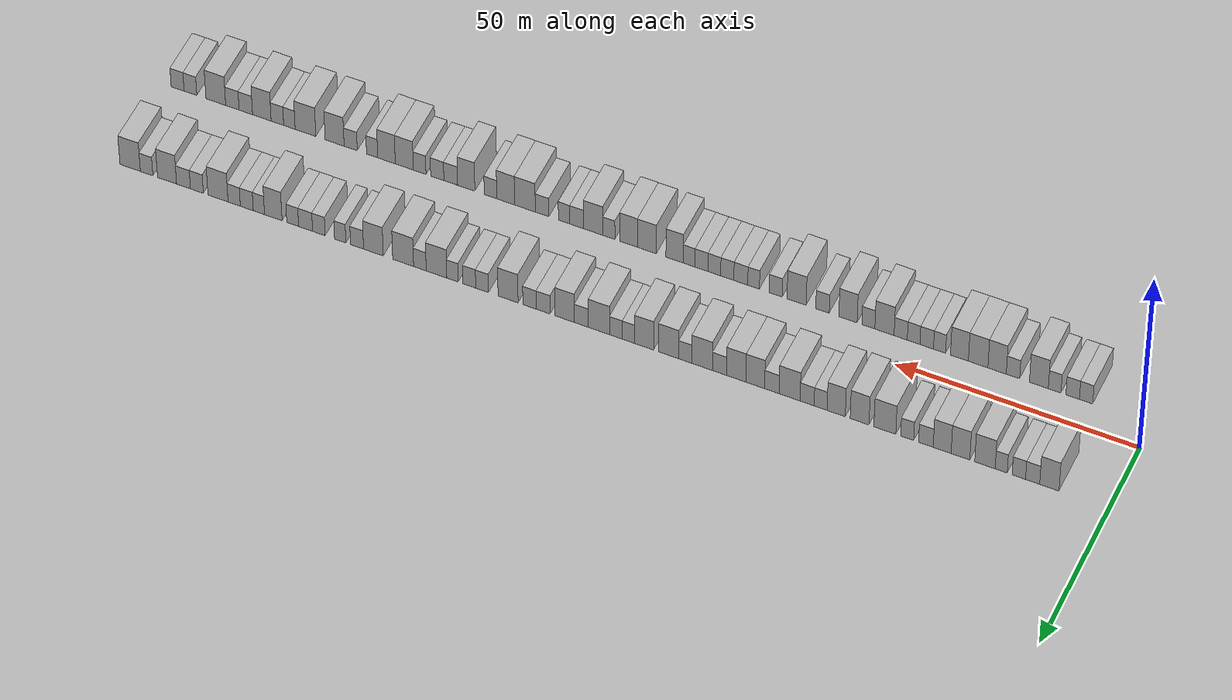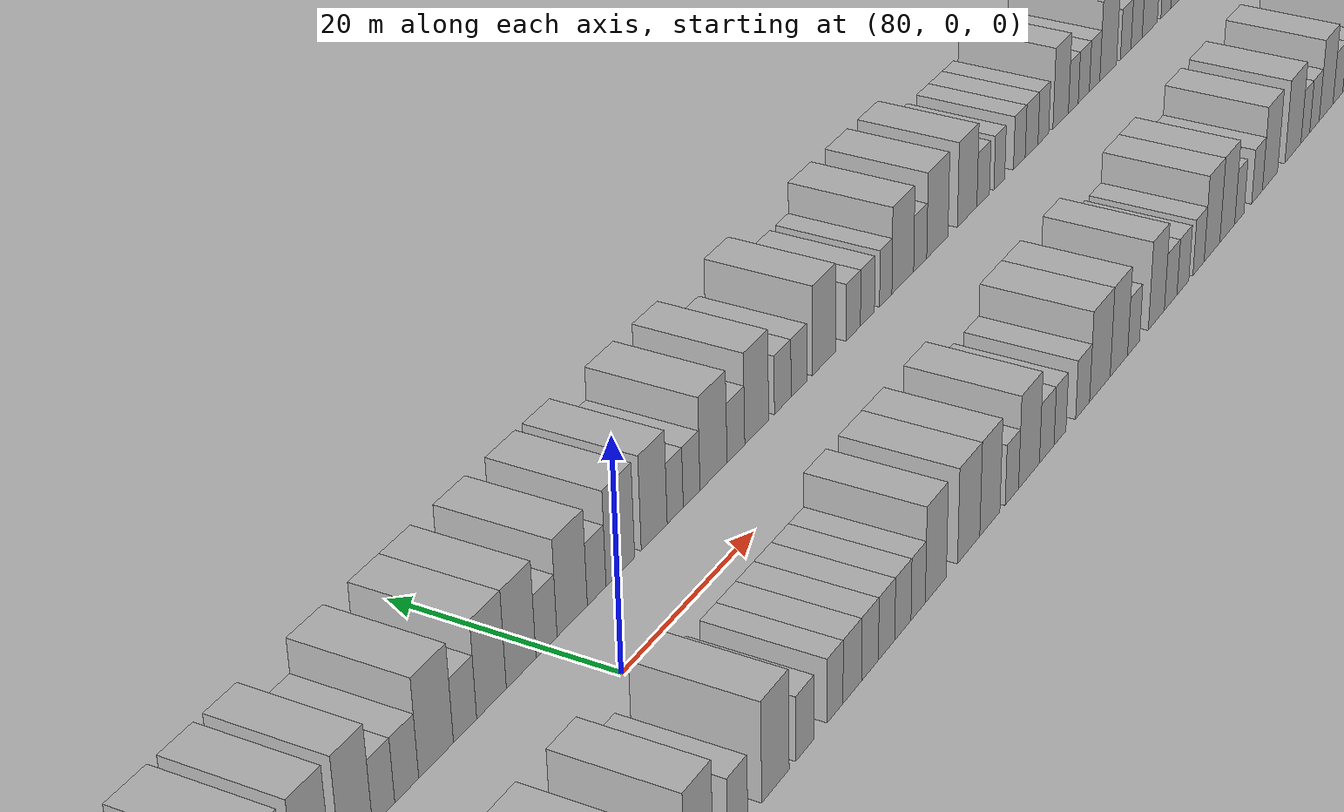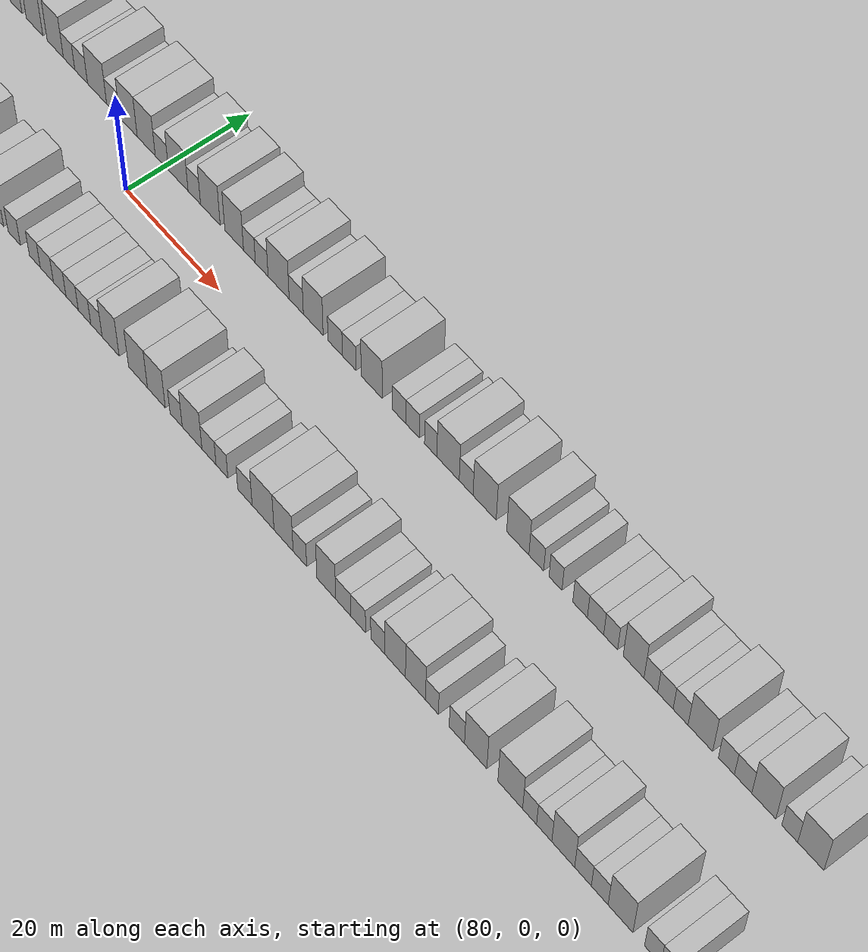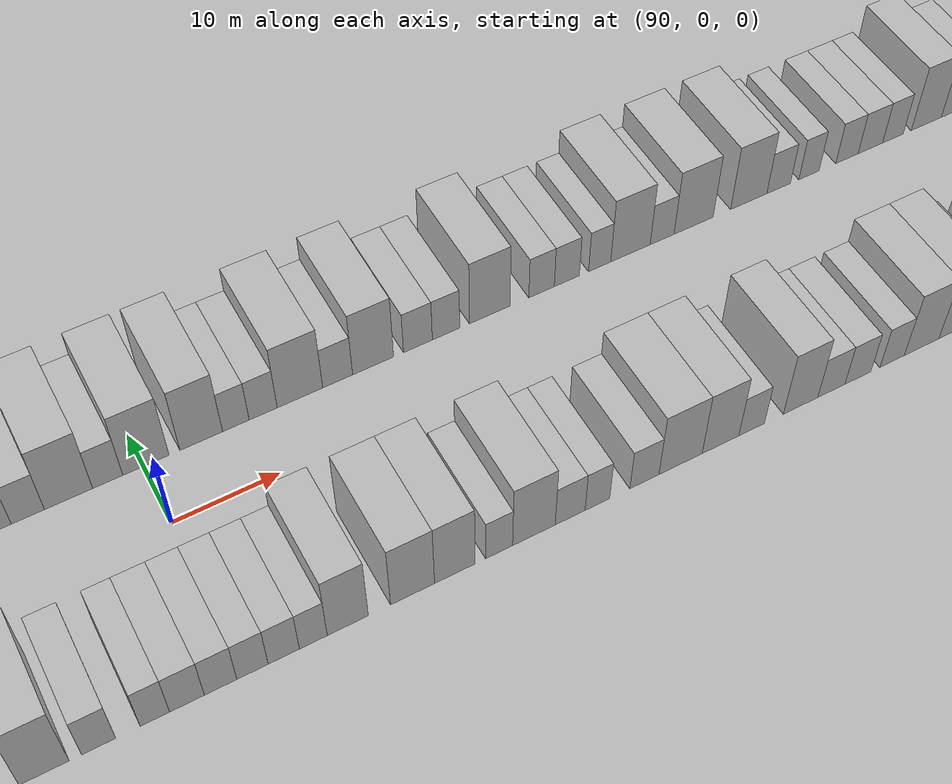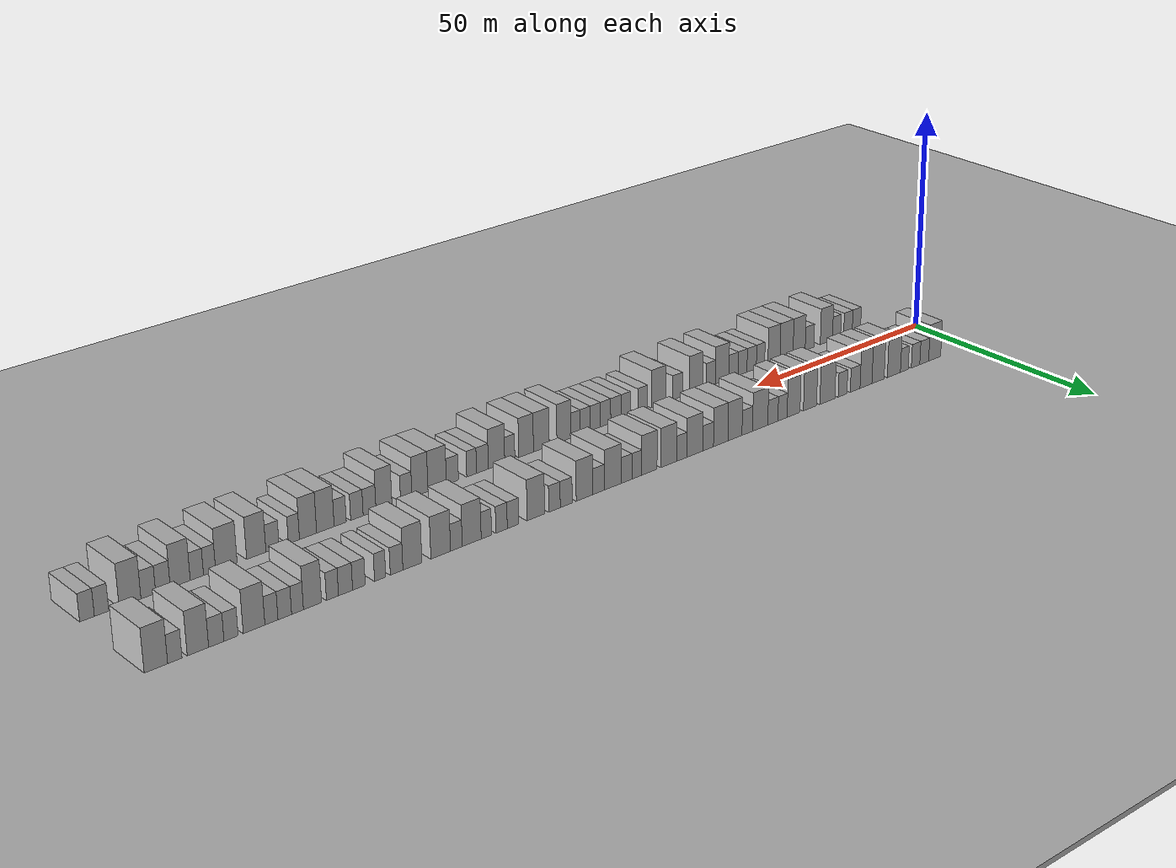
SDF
<?xml version="1.0" encoding="utf-8"?>

<sdf version="1.6">

   <world name="default">

      <gui fullscreen="0">

         <camera name="user_camera">

            <pose>-15 0 4.57585 0 0 0</pose>

            <view_controller>orbit</view_controller>

         </camera>

      </gui>

      <scene>

         <sky>

           <clouds>

             <speed>12</speed>

           </clouds>

         </sky>

         <ambient>0.4 0.4 0.4 1</ambient>

         <background>0.7 0.7 0.7 1</background>

         <shadows>1</shadows>

      </scene>

      <gravity>0 0 -9.8066</gravity>

      <magnetic_field>6e-06 2.3e-05 -4.2e-05</magnetic_field>

      <physics default="0" name="default_physics" type="ode">

         <ode>

            <solver>

               <type>quick</type>

               <iters>10</iters>

               <sor>1.0</sor>

               <use_dynamic_moi_rescaling>0</use_dynamic_moi_rescaling>

            </solver>

            <constraints>

               <cfm>0</cfm>

               <erp>0.2</erp>

               <contact_max_correcting_vel>100</contact_max_correcting_vel>

               <contact_surface_layer>0.001</contact_surface_layer>

            </constraints>

         </ode>

         <max_step_size>0.004</max_step_size>

         <real_time_factor>1</real_time_factor>

         <real_time_update_rate>250</real_time_update_rate>

      </physics>

      <light name="sun" type="directional">

         <cast_shadows>1</cast_shadows>

         <pose>0 0 10 0 0 0</pose>

         <diffuse>0.8 0.8 0.8 1</diffuse>

         <specular>0.2 0.2 0.2 1</specular>

         <attenuation>

            <range>1000</range>

            <constant>0.9</constant>

            <linear>0.01</linear>

            <quadratic>0.001</quadratic>

         </attenuation>

         <direction>-0.5 0.1 -0.9</direction>

      </light>

      <include>

         <name>ground_plane_1</name>

         <uri>model://HANNAS_ground_plane</uri>

         <pose>0 0 0  0 0 0</pose>

      </include>

      <include>

         <name>ground_plane_2</name>

         <uri>model://HANNAS_ground_plane</uri>

         <pose>100 0 0  0 0 0</pose>

      </include>

      <model name="building_1">

         <static>1</static>

         <pose frame="">11.9520 11.0000 0 0.000000 0.000000 1.570796</pose>

         <link name="link">

            <pose frame="">0 0 4.50 0 0 0</pose>

            <collision name="collision">

               <geometry>

                  <box>

                     <size>10.0000 3.9040 9.0000</size>

                  </box>

               </geometry>

               <max_contacts>10</max_contacts>

               <surface>

                  <contact>

                     <ode/>

                  </contact>

                  <bounce/>

                  <friction>

                     <torsional>

                        <ode/>

                     </torsional>

                     <ode/>

                  </friction>

               </surface>

            </collision>

            <visual name="visual">

               <cast_shadows>0</cast_shadows>

               <geometry>

                  <box>

                     <size>10.0000 3.9040 9.0000</size>

                  </box>

               </geometry>

               <material>

                  <script>

                     <uri>model://HANNAS_wall/materials/scripts</uri>

                     <uri>model://HANNAS_wall/materials/textures</uri>

                     <name>vrc/HANNAS_wall</name>

                  </script>

               </material>

            </visual>

            <self_collide>0</self_collide>

            <enable_wind>0</enable_wind>

            <kinematic>0</kinematic>

         </link>

      </model>

      <model name="building_2">

         <static>1</static>

         <pose frame="">15.3373 11.0000 0 0.000000 0.000000 1.570796</pose>

         <link name="link">

            <pose frame="">0 0 3.00 0 0 0</pose>

            <collision name="collision">

               <geometry>

                  <box>

                     <size>10.0000 2.8666 6.0000</size>

                  </box>

               </geometry>

               <max_contacts>10</max_contacts>

               <surface>

                  <contact>

                     <ode/>

                  </contact>

                  <bounce/>

                  <friction>

                     <torsional>

                        <ode/>

                     </torsional>

                     <ode/>

                  </friction>

               </surface>

            </collision>

            <visual name="visual">

               <cast_shadows>0</cast_shadows>

               <geometry>

                  <box>

                     <size>10.0000 2.8666 6.0000</size>

                  </box>

               </geometry>

               <material>

                  <script>

                     <uri>model://HANNAS_wall/materials/scripts</uri>

                     <uri>model://HANNAS_wall/materials/textures</uri>

                     <name>vrc/HANNAS_wall</name>

                  </script>

               </material>

            </visual>

            <self_collide>0</self_collide>

            <enable_wind>0</enable_wind>

            <kinematic>0</kinematic>

         </link>

      </model>

      <model name="building_3">

         <static>1</static>

         <pose frame="">18.1321 11.0000 0 0.000000 0.000000 1.570796</pose>

         <link name="link">

            <pose frame="">0 0 3.00 0 0 0</pose>

            <collision name="collision">

               <geometry>

                  <box>

                     <size>10.0000 2.7230 6.0000</size>

                  </box>

               </geometry>

               <max_contacts>10</max_contacts>

               <surface>

                  <contact>

                     <ode/>

                  </contact>

                  <bounce/>

                  <friction>

                     <torsional>

                        <ode/>

                     </torsional>

                     <ode/>

                  </friction>

               </surface>

            </collision>

            <visual name="visual">

               <cast_shadows>0</cast_shadows>

               <geometry>

                  <box>

                     <size>10.0000 2.7230 6.0000</size>

                  </box>

               </geometry>

               <material>

                  <script>

                     <uri>model://HANNAS_wall/materials/scripts</uri>

                     <uri>model://HANNAS_wall/materials/textures</uri>

                     <name>vrc/HANNAS_wall</name>

                  </script>

               </material>

            </visual>

            <self_collide>0</self_collide>

            <enable_wind>0</enable_wind>

            <kinematic>0</kinematic>

         </link>

      </model>

      <model name="building_4">

         <static>1</static>

         <pose frame="">21.7241 11.0000 0 0.000000 0.000000 1.570796</pose>

         <link name="link">

            <pose frame="">0 0 3.00 0 0 0</pose>

            <collision name="collision">

               <geometry>

                  <box>

                     <size>10.0000 2.4609 6.0000</size>

                  </box>

               </geometry>

               <max_contacts>10</max_contacts>

               <surface>

                  <contact>

                     <ode/>

                  </contact>

                  <bounce/>

                  <friction>

                     <torsional>

                        <ode/>

                     </torsional>

                     <ode/>

                  </friction>

               </surface>

            </collision>

            <visual name="visual">

               <cast_shadows>0</cast_shadows>

               <geometry>

                  <box>

                     <size>10.0000 2.4609 6.0000</size>

                  </box>

               </geometry>

               <material>

                  <script>

                     <uri>model://HANNAS_wall/materials/scripts</uri>

                     <uri>model://HANNAS_wall/materials/textures</uri>

                     <name>vrc/HANNAS_wall</name>

                  </script>

               </material>

            </visual>

            <self_collide>0</self_collide>

            <enable_wind>0</enable_wind>

            <kinematic>0</kinematic>

         </link>

      </model>

      <model name="building_5">

         <static>1</static>

         <pose frame="">25.0302 11.0000 0 0.000000 0.000000 1.570796</pose>

         <link name="link">

            <pose frame="">0 0 4.50 0 0 0</pose>

            <collision name="collision">

               <geometry>

                  <box>

                     <size>10.0000 4.1513 9.0000</size>

                  </box>

               </geometry>

               <max_contacts>10</max_contacts>

               <surface>

                  <contact>

                     <ode/>

                  </contact>

                  <bounce/>

                  <friction>

                     <torsional>

                        <ode/>

                     </torsional>

                     <ode/>

                  </friction>

               </surface>

            </collision>

            <visual name="visual">

               <cast_shadows>0</cast_shadows>

               <geometry>

                  <box>

                     <size>10.0000 4.1513 9.0000</size>

                  </box>

               </geometry>

               <material>

                  <script>

                     <uri>model://HANNAS_wall/materials/scripts</uri>

                     <uri>model://HANNAS_wall/materials/textures</uri>

                     <name>vrc/HANNAS_wall</name>

                  </script>

               </material>

            </visual>

            <self_collide>0</self_collide>

            <enable_wind>0</enable_wind>

            <kinematic>0</kinematic>

         </link>

      </model>

      <model name="building_6">

         <static>1</static>

         <pose frame="">30.0133 11.0000 0 0.000000 0.000000 1.570796</pose>

         <link name="link">

            <pose frame="">0 0 4.50 0 0 0</pose>

            <collision name="collision">

               <geometry>

                  <box>

                     <size>10.0000 3.8149 9.0000</size>

                  </box>

               </geometry>

               <max_contacts>10</max_contacts>

               <surface>

                  <contact>

                     <ode/>

                  </contact>

                  <bounce/>

                  <friction>

                     <torsional>

                        <ode/>

                     </torsional>

                     <ode/>

                  </friction>

               </surface>

            </collision>

            <visual name="visual">

               <cast_shadows>0</cast_shadows>

               <geometry>

                  <box>

                     <size>10.0000 3.8149 9.0000</size>

                  </box>

               </geometry>

               <material>

                  <script>

                     <uri>model://HANNAS_wall/materials/scripts</uri>

                     <uri>model://HANNAS_wall/materials/textures</uri>

                     <name>vrc/HANNAS_wall</name>

                  </script>

               </material>

            </visual>

            <self_collide>0</self_collide>

            <enable_wind>0</enable_wind>

            <kinematic>0</kinematic>

         </link>

      </model>

      <model name="building_7">

         <static>1</static>

         <pose frame="">33.7494 11.0000 0 0.000000 0.000000 1.570796</pose>

         <link name="link">

            <pose frame="">0 0 4.50 0 0 0</pose>

            <collision name="collision">

               <geometry>

                  <box>

                     <size>10.0000 3.6573 9.0000</size>

                  </box>

               </geometry>

               <max_contacts>10</max_contacts>

               <surface>

                  <contact>

                     <ode/>

                  </contact>

                  <bounce/>

                  <friction>

                     <torsional>

                        <ode/>

                     </torsional>

                     <ode/>

                  </friction>

               </surface>

            </collision>

            <visual name="visual">

               <cast_shadows>0</cast_shadows>

               <geometry>

                  <box>

                     <size>10.0000 3.6573 9.0000</size>

                  </box>

               </geometry>

               <material>

                  <script>

                     <uri>model://HANNAS_wall/materials/scripts</uri>

                     <uri>model://HANNAS_wall/materials/textures</uri>

                     <name>vrc/HANNAS_wall</name>

                  </script>

               </material>

            </visual>

            <self_collide>0</self_collide>

            <enable_wind>0</enable_wind>

            <kinematic>0</kinematic>

         </link>

      </model>

      <model name="building_8">

         <static>1</static>

         <pose frame="">37.0728 11.0000 0 0.000000 0.000000 1.570796</pose>

         <link name="link">

            <pose frame="">0 0 3.00 0 0 0</pose>

            <collision name="collision">

               <geometry>

                  <box>

                     <size>10.0000 2.9895 6.0000</size>

                  </box>

               </geometry>

               <max_contacts>10</max_contacts>

               <surface>

                  <contact>

                     <ode/>

                  </contact>

                  <bounce/>

                  <friction>

                     <torsional>

                        <ode/>

                     </torsional>

                     <ode/>

                  </friction>

               </surface>

            </collision>

            <visual name="visual">

               <cast_shadows>0</cast_shadows>

               <geometry>

                  <box>

                     <size>10.0000 2.9895 6.0000</size>

                  </box>

               </geometry>

               <material>

                  <script>

                     <uri>model://HANNAS_wall/materials/scripts</uri>

                     <uri>model://HANNAS_wall/materials/textures</uri>

                     <name>vrc/HANNAS_wall</name>

                  </script>

               </material>

            </visual>

            <self_collide>0</self_collide>

            <enable_wind>0</enable_wind>

            <kinematic>0</kinematic>

         </link>

      </model>

      <model name="building_9">

         <static>1</static>

         <pose frame="">40.8985 11.0000 0 0.000000 0.000000 1.570796</pose>

         <link name="link">

            <pose frame="">0 0 3.00 0 0 0</pose>

            <collision name="collision">

               <geometry>

                  <box>

                     <size>10.0000 2.6618 6.0000</size>

                  </box>

               </geometry>

               <max_contacts>10</max_contacts>

               <surface>

                  <contact>

                     <ode/>

                  </contact>

                  <bounce/>

                  <friction>

                     <torsional>

                        <ode/>

                     </torsional>

                     <ode/>

                  </friction>

               </surface>

            </collision>

            <visual name="visual">

               <cast_shadows>0</cast_shadows>

               <geometry>

                  <box>

                     <size>10.0000 2.6618 6.0000</size>

                  </box>

               </geometry>

               <material>

                  <script>

                     <uri>model://HANNAS_wall/materials/scripts</uri>

                     <uri>model://HANNAS_wall/materials/textures</uri>

                     <name>vrc/HANNAS_wall</name>

                  </script>

               </material>

            </visual>

            <self_collide>0</self_collide>

            <enable_wind>0</enable_wind>

            <kinematic>0</kinematic>

         </link>

      </model>

      <model name="building_10">

         <static>1</static>

         <pose frame="">45.4776 11.0000 0 0.000000 0.000000 1.570796</pose>

         <link name="link">

            <pose frame="">0 0 4.50 0 0 0</pose>

            <collision name="collision">

               <geometry>

                  <box>

                     <size>10.0000 4.4963 9.0000</size>

                  </box>

               </geometry>

               <max_contacts>10</max_contacts>

               <surface>

                  <contact>

                     <ode/>

                  </contact>

                  <bounce/>

                  <friction>

                     <torsional>

                        <ode/>

                     </torsional>

                     <ode/>

                  </friction>

               </surface>

            </collision>

            <visual name="visual">

               <cast_shadows>0</cast_shadows>

               <geometry>

                  <box>

                     <size>10.0000 4.4963 9.0000</size>

                  </box>

               </geometry>

               <material>

                  <script>

                     <uri>model://HANNAS_wall/materials/scripts</uri>

                     <uri>model://HANNAS_wall/materials/textures</uri>

                     <name>vrc/HANNAS_wall</name>

                  </script>

               </material>

            </visual>

            <self_collide>0</self_collide>

            <enable_wind>0</enable_wind>

            <kinematic>0</kinematic>

         </link>

      </model>

      <model name="building_11">

         <static>1</static>

         <pose frame="">50.6622 11.0000 0 0.000000 0.000000 1.570796</pose>

         <link name="link">

            <pose frame="">0 0 4.50 0 0 0</pose>

            <collision name="collision">

               <geometry>

                  <box>

                     <size>10.0000 3.8730 9.0000</size>

                  </box>

               </geometry>

               <max_contacts>10</max_contacts>

               <surface>

                  <contact>

                     <ode/>

                  </contact>

                  <bounce/>

                  <friction>

                     <torsional>

                        <ode/>

                     </torsional>

                     <ode/>

                  </friction>

               </surface>

            </collision>

            <visual name="visual">

               <cast_shadows>0</cast_shadows>

               <geometry>

                  <box>

                     <size>10.0000 3.8730 9.0000</size>

                  </box>

               </geometry>

               <material>

                  <script>

                     <uri>model://HANNAS_wall/materials/scripts</uri>

                     <uri>model://HANNAS_wall/materials/textures</uri>

                     <name>vrc/HANNAS_wall</name>

                  </script>

               </material>

            </visual>

            <self_collide>0</self_collide>

            <enable_wind>0</enable_wind>

            <kinematic>0</kinematic>

         </link>

      </model>

      <model name="building_12">

         <static>1</static>

         <pose frame="">55.4799 11.0000 0 0.000000 0.000000 1.570796</pose>

         <link name="link">

            <pose frame="">0 0 4.50 0 0 0</pose>

            <collision name="collision">

               <geometry>

                  <box>

                     <size>10.0000 3.7623 9.0000</size>

                  </box>

               </geometry>

               <max_contacts>10</max_contacts>

               <surface>

                  <contact>

                     <ode/>

                  </contact>

                  <bounce/>

                  <friction>

                     <torsional>

                        <ode/>

                     </torsional>

                     <ode/>

                  </friction>

               </surface>

            </collision>

            <visual name="visual">

               <cast_shadows>0</cast_shadows>

               <geometry>

                  <box>

                     <size>10.0000 3.7623 9.0000</size>

                  </box>

               </geometry>

               <material>

                  <script>

                     <uri>model://HANNAS_wall/materials/scripts</uri>

                     <uri>model://HANNAS_wall/materials/textures</uri>

                     <name>vrc/HANNAS_wall</name>

                  </script>

               </material>

            </visual>

            <self_collide>0</self_collide>

            <enable_wind>0</enable_wind>

            <kinematic>0</kinematic>

         </link>

      </model>

      <model name="building_13">

         <static>1</static>

         <pose frame="">58.6857 11.0000 0 0.000000 0.000000 1.570796</pose>

         <link name="link">

            <pose frame="">0 0 3.00 0 0 0</pose>

            <collision name="collision">

               <geometry>

                  <box>

                     <size>10.0000 2.6495 6.0000</size>

                  </box>

               </geometry>

               <max_contacts>10</max_contacts>

               <surface>

                  <contact>

                     <ode/>

                  </contact>

                  <bounce/>

                  <friction>

                     <torsional>

                        <ode/>

                     </torsional>

                     <ode/>

                  </friction>

               </surface>

            </collision>

            <visual name="visual">

               <cast_shadows>0</cast_shadows>

               <geometry>

                  <box>

                     <size>10.0000 2.6495 6.0000</size>

                  </box>

               </geometry>

               <material>

                  <script>

                     <uri>model://HANNAS_wall/materials/scripts</uri>

                     <uri>model://HANNAS_wall/materials/textures</uri>

                     <name>vrc/HANNAS_wall</name>

                  </script>

               </material>

            </visual>

            <self_collide>0</self_collide>

            <enable_wind>0</enable_wind>

            <kinematic>0</kinematic>

         </link>

      </model>

      <model name="building_14">

         <static>1</static>

         <pose frame="">61.4664 11.0000 0 0.000000 0.000000 1.570796</pose>

         <link name="link">

            <pose frame="">0 0 3.00 0 0 0</pose>

            <collision name="collision">

               <geometry>

                  <box>

                     <size>10.0000 2.9119 6.0000</size>

                  </box>

               </geometry>

               <max_contacts>10</max_contacts>

               <surface>

                  <contact>

                     <ode/>

                  </contact>

                  <bounce/>

                  <friction>

                     <torsional>

                        <ode/>

                     </torsional>

                     <ode/>

                  </friction>

               </surface>

            </collision>

            <visual name="visual">

               <cast_shadows>0</cast_shadows>

               <geometry>

                  <box>

                     <size>10.0000 2.9119 6.0000</size>

                  </box>

               </geometry>

               <material>

                  <script>

                     <uri>model://HANNAS_wall/materials/scripts</uri>

                     <uri>model://HANNAS_wall/materials/textures</uri>

                     <name>vrc/HANNAS_wall</name>

                  </script>

               </material>

            </visual>

            <self_collide>0</self_collide>

            <enable_wind>0</enable_wind>

            <kinematic>0</kinematic>

         </link>

      </model>

      <model name="building_15">

         <static>1</static>

         <pose frame="">65.0920 11.0000 0 0.000000 0.000000 1.570796</pose>

         <link name="link">

            <pose frame="">0 0 4.50 0 0 0</pose>

            <collision name="collision">

               <geometry>

                  <box>

                     <size>10.0000 4.3392 9.0000</size>

                  </box>

               </geometry>

               <max_contacts>10</max_contacts>

               <surface>

                  <contact>

                     <ode/>

                  </contact>

                  <bounce/>

                  <friction>

                     <torsional>

                        <ode/>

                     </torsional>

                     <ode/>

                  </friction>

               </surface>

            </collision>

            <visual name="visual">

               <cast_shadows>0</cast_shadows>

               <geometry>

                  <box>

                     <size>10.0000 4.3392 9.0000</size>

                  </box>

               </geometry>

               <material>

                  <script>

                     <uri>model://HANNAS_wall/materials/scripts</uri>

                     <uri>model://HANNAS_wall/materials/textures</uri>

                     <name>vrc/HANNAS_wall</name>

                  </script>

               </material>

            </visual>

            <self_collide>0</self_collide>

            <enable_wind>0</enable_wind>

            <kinematic>0</kinematic>

         </link>

      </model>

      <model name="building_16">

         <static>1</static>

         <pose frame="">68.7503 11.0000 0 0.000000 0.000000 1.570796</pose>

         <link name="link">

            <pose frame="">0 0 3.00 0 0 0</pose>

            <collision name="collision">

               <geometry>

                  <box>

                     <size>10.0000 2.9774 6.0000</size>

                  </box>

               </geometry>

               <max_contacts>10</max_contacts>

               <surface>

                  <contact>

                     <ode/>

                  </contact>

                  <bounce/>

                  <friction>

                     <torsional>

                        <ode/>

                     </torsional>

                     <ode/>

                  </friction>

               </surface>

            </collision>

            <visual name="visual">

               <cast_shadows>0</cast_shadows>

               <geometry>

                  <box>

                     <size>10.0000 2.9774 6.0000</size>

                  </box>

               </geometry>

               <material>

                  <script>

                     <uri>model://HANNAS_wall/materials/scripts</uri>

                     <uri>model://HANNAS_wall/materials/textures</uri>

                     <name>vrc/HANNAS_wall</name>

                  </script>

               </material>

            </visual>

            <self_collide>0</self_collide>

            <enable_wind>0</enable_wind>

            <kinematic>0</kinematic>

         </link>

      </model>

      <model name="building_17">

         <static>1</static>

         <pose frame="">72.1875 11.0000 0 0.000000 0.000000 1.570796</pose>

         <link name="link">

            <pose frame="">0 0 4.50 0 0 0</pose>

            <collision name="collision">

               <geometry>

                  <box>

                     <size>10.0000 3.8970 9.0000</size>

                  </box>

               </geometry>

               <max_contacts>10</max_contacts>

               <surface>

                  <contact>

                     <ode/>

                  </contact>

                  <bounce/>

                  <friction>

                     <torsional>

                        <ode/>

                     </torsional>

                     <ode/>

                  </friction>

               </surface>

            </collision>

            <visual name="visual">

               <cast_shadows>0</cast_shadows>

               <geometry>

                  <box>

                     <size>10.0000 3.8970 9.0000</size>

                  </box>

               </geometry>

               <material>

                  <script>

                     <uri>model://HANNAS_wall/materials/scripts</uri>

                     <uri>model://HANNAS_wall/materials/textures</uri>

                     <name>vrc/HANNAS_wall</name>

                  </script>

               </material>

            </visual>

            <self_collide>0</self_collide>

            <enable_wind>0</enable_wind>

            <kinematic>0</kinematic>

         </link>

      </model>

      <model name="building_18">

         <static>1</static>

         <pose frame="">76.1417 11.0000 0 0.000000 0.000000 1.570796</pose>

         <link name="link">

            <pose frame="">0 0 4.50 0 0 0</pose>

            <collision name="collision">

               <geometry>

                  <box>

                     <size>10.0000 4.0115 9.0000</size>

                  </box>

               </geometry>

               <max_contacts>10</max_contacts>

               <surface>

                  <contact>

                     <ode/>

                  </contact>

                  <bounce/>

                  <friction>

                     <torsional>

                        <ode/>

                     </torsional>

                     <ode/>

                  </friction>

               </surface>

            </collision>

            <visual name="visual">

               <cast_shadows>0</cast_shadows>

               <geometry>

                  <box>

                     <size>10.0000 4.0115 9.0000</size>

                  </box>

               </geometry>

               <material>

                  <script>

                     <uri>model://HANNAS_wall/materials/scripts</uri>

                     <uri>model://HANNAS_wall/materials/textures</uri>

                     <name>vrc/HANNAS_wall</name>

                  </script>

               </material>

            </visual>

            <self_collide>0</self_collide>

            <enable_wind>0</enable_wind>

            <kinematic>0</kinematic>

         </link>

      </model>

      <model name="building_19">

         <static>1</static>

         <pose frame="">79.6053 11.0000 0 0.000000 0.000000 1.570796</pose>

         <link name="link">

            <pose frame="">0 0 3.00 0 0 0</pose>

            <collision name="collision">

               <geometry>

                  <box>

                     <size>10.0000 2.9156 6.0000</size>

                  </box>

               </geometry>

               <max_contacts>10</max_contacts>

               <surface>

                  <contact>

                     <ode/>

                  </contact>

                  <bounce/>

                  <friction>

                     <torsional>

                        <ode/>

                     </torsional>

                     <ode/>

                  </friction>

               </surface>

            </collision>

            <visual name="visual">

               <cast_shadows>0</cast_shadows>

               <geometry>

                  <box>

                     <size>10.0000 2.9156 6.0000</size>

                  </box>

               </geometry>

               <material>

                  <script>

                     <uri>model://HANNAS_wall/materials/scripts</uri>

                     <uri>model://HANNAS_wall/materials/textures</uri>

                     <name>vrc/HANNAS_wall</name>

                  </script>

               </material>

            </visual>

            <self_collide>0</self_collide>

            <enable_wind>0</enable_wind>

            <kinematic>0</kinematic>

         </link>

      </model>

      <model name="building_20">

         <static>1</static>

         <pose frame="">83.2097 11.0000 0 0.000000 0.000000 1.570796</pose>

         <link name="link">

            <pose frame="">0 0 4.50 0 0 0</pose>

            <collision name="collision">

               <geometry>

                  <box>

                     <size>10.0000 4.2931 9.0000</size>

                  </box>

               </geometry>

               <max_contacts>10</max_contacts>

               <surface>

                  <contact>

                     <ode/>

                  </contact>

                  <bounce/>

                  <friction>

                     <torsional>

                        <ode/>

                     </torsional>

                     <ode/>

                  </friction>

               </surface>

            </collision>

            <visual name="visual">

               <cast_shadows>0</cast_shadows>

               <geometry>

                  <box>

                     <size>10.0000 4.2931 9.0000</size>

                  </box>

               </geometry>

               <material>

                  <script>

                     <uri>model://HANNAS_wall/materials/scripts</uri>

                     <uri>model://HANNAS_wall/materials/textures</uri>

                     <name>vrc/HANNAS_wall</name>

                  </script>

               </material>

            </visual>

            <self_collide>0</self_collide>

            <enable_wind>0</enable_wind>

            <kinematic>0</kinematic>

         </link>

      </model>

      <model name="building_21">

         <static>1</static>

         <pose frame="">86.7155 11.0000 0 0.000000 0.000000 1.570796</pose>

         <link name="link">

            <pose frame="">0 0 3.00 0 0 0</pose>

            <collision name="collision">

               <geometry>

                  <box>

                     <size>10.0000 2.7185 6.0000</size>

                  </box>

               </geometry>

               <max_contacts>10</max_contacts>

               <surface>

                  <contact>

                     <ode/>

                  </contact>

                  <bounce/>

                  <friction>

                     <torsional>

                        <ode/>

                     </torsional>

                     <ode/>

                  </friction>

               </surface>

            </collision>

            <visual name="visual">

               <cast_shadows>0</cast_shadows>

               <geometry>

                  <box>

                     <size>10.0000 2.7185 6.0000</size>

                  </box>

               </geometry>

               <material>

                  <script>

                     <uri>model://HANNAS_wall/materials/scripts</uri>

                     <uri>model://HANNAS_wall/materials/textures</uri>

                     <name>vrc/HANNAS_wall</name>

                  </script>

               </material>

            </visual>

            <self_collide>0</self_collide>

            <enable_wind>0</enable_wind>

            <kinematic>0</kinematic>

         </link>

      </model>

      <model name="building_22">

         <static>1</static>

         <pose frame="">90.1966 11.0000 0 0.000000 0.000000 1.570796</pose>

         <link name="link">

            <pose frame="">0 0 4.50 0 0 0</pose>

            <collision name="collision">

               <geometry>

                  <box>

                     <size>10.0000 4.2436 9.0000</size>

                  </box>

               </geometry>

               <max_contacts>10</max_contacts>

               <surface>

                  <contact>

                     <ode/>

                  </contact>

                  <bounce/>

                  <friction>

                     <torsional>

                        <ode/>

                     </torsional>

                     <ode/>

                  </friction>

               </surface>

            </collision>

            <visual name="visual">

               <cast_shadows>0</cast_shadows>

               <geometry>

                  <box>

                     <size>10.0000 4.2436 9.0000</size>

                  </box>

               </geometry>

               <material>

                  <script>

                     <uri>model://HANNAS_wall/materials/scripts</uri>

                     <uri>model://HANNAS_wall/materials/textures</uri>

                     <name>vrc/HANNAS_wall</name>

                  </script>

               </material>

            </visual>

            <self_collide>0</self_collide>

            <enable_wind>0</enable_wind>

            <kinematic>0</kinematic>

         </link>

      </model>

      <model name="building_23">

         <static>1</static>

         <pose frame="">95.3163 11.0000 0 0.000000 0.000000 1.570796</pose>

         <link name="link">

            <pose frame="">0 0 4.50 0 0 0</pose>

            <collision name="collision">

               <geometry>

                  <box>

                     <size>10.0000 3.9959 9.0000</size>

                  </box>

               </geometry>

               <max_contacts>10</max_contacts>

               <surface>

                  <contact>

                     <ode/>

                  </contact>

                  <bounce/>

                  <friction>

                     <torsional>

                        <ode/>

                     </torsional>

                     <ode/>

                  </friction>

               </surface>

            </collision>

            <visual name="visual">

               <cast_shadows>0</cast_shadows>

               <geometry>

                  <box>

                     <size>10.0000 3.9959 9.0000</size>

                  </box>

               </geometry>

               <material>

                  <script>

                     <uri>model://HANNAS_wall/materials/scripts</uri>

                     <uri>model://HANNAS_wall/materials/textures</uri>

                     <name>vrc/HANNAS_wall</name>

                  </script>

               </material>

            </visual>

            <self_collide>0</self_collide>

            <enable_wind>0</enable_wind>

            <kinematic>0</kinematic>

         </link>

      </model>

      <model name="building_24">

         <static>1</static>

         <pose frame="">98.5761 11.0000 0 0.000000 0.000000 1.570796</pose>

         <link name="link">

            <pose frame="">0 0 3.00 0 0 0</pose>

            <collision name="collision">

               <geometry>

                  <box>

                     <size>10.0000 2.5237 6.0000</size>

                  </box>

               </geometry>

               <max_contacts>10</max_contacts>

               <surface>

                  <contact>

                     <ode/>

                  </contact>

                  <bounce/>

                  <friction>

                     <torsional>

                        <ode/>

                     </torsional>

                     <ode/>

                  </friction>

               </surface>

            </collision>

            <visual name="visual">

               <cast_shadows>0</cast_shadows>

               <geometry>

                  <box>

                     <size>10.0000 2.5237 6.0000</size>

                  </box>

               </geometry>

               <material>

                  <script>

                     <uri>model://HANNAS_wall/materials/scripts</uri>

                     <uri>model://HANNAS_wall/materials/textures</uri>

                     <name>vrc/HANNAS_wall</name>

                  </script>

               </material>

            </visual>

            <self_collide>0</self_collide>

            <enable_wind>0</enable_wind>

            <kinematic>0</kinematic>

         </link>

      </model>

      <model name="building_25">

         <static>1</static>

         <pose frame="">101.1797 11.0000 0 0.000000 0.000000 1.570796</pose>

         <link name="link">

            <pose frame="">0 0 3.00 0 0 0</pose>

            <collision name="collision">

               <geometry>

                  <box>

                     <size>10.0000 2.6833 6.0000</size>

                  </box>

               </geometry>

               <max_contacts>10</max_contacts>

               <surface>

                  <contact>

                     <ode/>

                  </contact>

                  <bounce/>

                  <friction>

                     <torsional>

                        <ode/>

                     </torsional>

                     <ode/>

                  </friction>

               </surface>

            </collision>

            <visual name="visual">

               <cast_shadows>0</cast_shadows>

               <geometry>

                  <box>

                     <size>10.0000 2.6833 6.0000</size>

                  </box>

               </geometry>

               <material>

                  <script>

                     <uri>model://HANNAS_wall/materials/scripts</uri>

                     <uri>model://HANNAS_wall/materials/textures</uri>

                     <name>vrc/HANNAS_wall</name>

                  </script>

               </material>

            </visual>

            <self_collide>0</self_collide>

            <enable_wind>0</enable_wind>

            <kinematic>0</kinematic>

         </link>

      </model>

      <model name="building_26">

         <static>1</static>

         <pose frame="">104.7301 11.0000 0 0.000000 0.000000 1.570796</pose>

         <link name="link">

            <pose frame="">0 0 4.50 0 0 0</pose>

            <collision name="collision">

               <geometry>

                  <box>

                     <size>10.0000 4.4175 9.0000</size>

                  </box>

               </geometry>

               <max_contacts>10</max_contacts>

               <surface>

                  <contact>

                     <ode/>

                  </contact>

                  <bounce/>

                  <friction>

                     <torsional>

                        <ode/>

                     </torsional>

                     <ode/>

                  </friction>

               </surface>

            </collision>

            <visual name="visual">

               <cast_shadows>0</cast_shadows>

               <geometry>

                  <box>

                     <size>10.0000 4.4175 9.0000</size>

                  </box>

               </geometry>

               <material>

                  <script>

                     <uri>model://HANNAS_wall/materials/scripts</uri>

                     <uri>model://HANNAS_wall/materials/textures</uri>

                     <name>vrc/HANNAS_wall</name>

                  </script>

               </material>

            </visual>

            <self_collide>0</self_collide>

            <enable_wind>0</enable_wind>

            <kinematic>0</kinematic>

         </link>

      </model>

      <model name="building_27">

         <static>1</static>

         <pose frame="">108.4140 11.0000 0 0.000000 0.000000 1.570796</pose>

         <link name="link">

            <pose frame="">0 0 3.00 0 0 0</pose>

            <collision name="collision">

               <geometry>

                  <box>

                     <size>10.0000 2.9504 6.0000</size>

                  </box>

               </geometry>

               <max_contacts>10</max_contacts>

               <surface>

                  <contact>

                     <ode/>

                  </contact>

                  <bounce/>

                  <friction>

                     <torsional>

                        <ode/>

                     </torsional>

                     <ode/>

                  </friction>

               </surface>

            </collision>

            <visual name="visual">

               <cast_shadows>0</cast_shadows>

               <geometry>

                  <box>

                     <size>10.0000 2.9504 6.0000</size>

                  </box>

               </geometry>

               <material>

                  <script>

                     <uri>model://HANNAS_wall/materials/scripts</uri>

                     <uri>model://HANNAS_wall/materials/textures</uri>

                     <name>vrc/HANNAS_wall</name>

                  </script>

               </material>

            </visual>

            <self_collide>0</self_collide>

            <enable_wind>0</enable_wind>

            <kinematic>0</kinematic>

         </link>

      </model>

      <model name="building_28">

         <static>1</static>

         <pose frame="">111.9314 11.0000 0 0.000000 0.000000 1.570796</pose>

         <link name="link">

            <pose frame="">0 0 4.50 0 0 0</pose>

            <collision name="collision">

               <geometry>

                  <box>

                     <size>10.0000 4.0844 9.0000</size>

                  </box>

               </geometry>

               <max_contacts>10</max_contacts>

               <surface>

                  <contact>

                     <ode/>

                  </contact>

                  <bounce/>

                  <friction>

                     <torsional>

                        <ode/>

                     </torsional>

                     <ode/>

                  </friction>

               </surface>

            </collision>

            <visual name="visual">

               <cast_shadows>0</cast_shadows>

               <geometry>

                  <box>

                     <size>10.0000 4.0844 9.0000</size>

                  </box>

               </geometry>

               <material>

                  <script>

                     <uri>model://HANNAS_wall/materials/scripts</uri>

                     <uri>model://HANNAS_wall/materials/textures</uri>

                     <name>vrc/HANNAS_wall</name>

                  </script>

               </material>

            </visual>

            <self_collide>0</self_collide>

            <enable_wind>0</enable_wind>

            <kinematic>0</kinematic>

         </link>

      </model>

      <model name="building_29">

         <static>1</static>

         <pose frame="">116.4413 11.0000 0 0.000000 0.000000 1.570796</pose>

         <link name="link">

            <pose frame="">0 0 3.00 0 0 0</pose>

            <collision name="collision">

               <geometry>

                  <box>

                     <size>10.0000 2.9353 6.0000</size>

                  </box>

               </geometry>

               <max_contacts>10</max_contacts>

               <surface>

                  <contact>

                     <ode/>

                  </contact>

                  <bounce/>

                  <friction>

                     <torsional>

                        <ode/>

                     </torsional>

                     <ode/>

                  </friction>

               </surface>

            </collision>

            <visual name="visual">

               <cast_shadows>0</cast_shadows>

               <geometry>

                  <box>

                     <size>10.0000 2.9353 6.0000</size>

                  </box>

               </geometry>

               <material>

                  <script>

                     <uri>model://HANNAS_wall/materials/scripts</uri>

                     <uri>model://HANNAS_wall/materials/textures</uri>

                     <name>vrc/HANNAS_wall</name>

                  </script>

               </material>

            </visual>

            <self_collide>0</self_collide>

            <enable_wind>0</enable_wind>

            <kinematic>0</kinematic>

         </link>

      </model>

      <model name="building_30">

         <static>1</static>

         <pose frame="">119.3154 11.0000 0 0.000000 0.000000 1.570796</pose>

         <link name="link">

            <pose frame="">0 0 3.00 0 0 0</pose>

            <collision name="collision">

               <geometry>

                  <box>

                     <size>10.0000 2.8128 6.0000</size>

                  </box>

               </geometry>

               <max_contacts>10</max_contacts>

               <surface>

                  <contact>

                     <ode/>

                  </contact>

                  <bounce/>

                  <friction>

                     <torsional>

                        <ode/>

                     </torsional>

                     <ode/>

                  </friction>

               </surface>

            </collision>

            <visual name="visual">

               <cast_shadows>0</cast_shadows>

               <geometry>

                  <box>

                     <size>10.0000 2.8128 6.0000</size>

                  </box>

               </geometry>

               <material>

                  <script>

                     <uri>model://HANNAS_wall/materials/scripts</uri>

                     <uri>model://HANNAS_wall/materials/textures</uri>

                     <name>vrc/HANNAS_wall</name>

                  </script>

               </material>

            </visual>

            <self_collide>0</self_collide>

            <enable_wind>0</enable_wind>

            <kinematic>0</kinematic>

         </link>

      </model>

      <model name="building_31">

         <static>1</static>

         <pose frame="">123.8374 11.0000 0 0.000000 0.000000 1.570796</pose>

         <link name="link">

            <pose frame="">0 0 4.50 0 0 0</pose>

            <collision name="collision">

               <geometry>

                  <box>

                     <size>10.0000 4.2310 9.0000</size>

                  </box>

               </geometry>

               <max_contacts>10</max_contacts>

               <surface>

                  <contact>

                     <ode/>

                  </contact>

                  <bounce/>

                  <friction>

                     <torsional>

                        <ode/>

                     </torsional>

                     <ode/>

                  </friction>

               </surface>

            </collision>

            <visual name="visual">

               <cast_shadows>0</cast_shadows>

               <geometry>

                  <box>

                     <size>10.0000 4.2310 9.0000</size>

                  </box>

               </geometry>

               <material>

                  <script>

                     <uri>model://HANNAS_wall/materials/scripts</uri>

                     <uri>model://HANNAS_wall/materials/textures</uri>

                     <name>vrc/HANNAS_wall</name>

                  </script>

               </material>

            </visual>

            <self_collide>0</self_collide>

            <enable_wind>0</enable_wind>

            <kinematic>0</kinematic>

         </link>

      </model>

      <model name="building_32">

         <static>1</static>

         <pose frame="">129.3143 11.0000 0 0.000000 0.000000 1.570796</pose>

         <link name="link">

            <pose frame="">0 0 3.00 0 0 0</pose>

            <collision name="collision">

               <geometry>

                  <box>

                     <size>10.0000 2.7228 6.0000</size>

                  </box>

               </geometry>

               <max_contacts>10</max_contacts>

               <surface>

                  <contact>

                     <ode/>

                  </contact>

                  <bounce/>

                  <friction>

                     <torsional>

                        <ode/>

                     </torsional>

                     <ode/>

                  </friction>

               </surface>

            </collision>

            <visual name="visual">

               <cast_shadows>0</cast_shadows>

               <geometry>

                  <box>

                     <size>10.0000 2.7228 6.0000</size>

                  </box>

               </geometry>

               <material>

                  <script>

                     <uri>model://HANNAS_wall/materials/scripts</uri>

                     <uri>model://HANNAS_wall/materials/textures</uri>

                     <name>vrc/HANNAS_wall</name>

                  </script>

               </material>

            </visual>

            <self_collide>0</self_collide>

            <enable_wind>0</enable_wind>

            <kinematic>0</kinematic>

         </link>

      </model>

      <model name="building_33">

         <static>1</static>

         <pose frame="">132.0238 11.0000 0 0.000000 0.000000 1.570796</pose>

         <link name="link">

            <pose frame="">0 0 3.00 0 0 0</pose>

            <collision name="collision">

               <geometry>

                  <box>

                     <size>10.0000 2.6963 6.0000</size>

                  </box>

               </geometry>

               <max_contacts>10</max_contacts>

               <surface>

                  <contact>

                     <ode/>

                  </contact>

                  <bounce/>

                  <friction>

                     <torsional>

                        <ode/>

                     </torsional>

                     <ode/>

                  </friction>

               </surface>

            </collision>

            <visual name="visual">

               <cast_shadows>0</cast_shadows>

               <geometry>

                  <box>

                     <size>10.0000 2.6963 6.0000</size>

                  </box>

               </geometry>

               <material>

                  <script>

                     <uri>model://HANNAS_wall/materials/scripts</uri>

                     <uri>model://HANNAS_wall/materials/textures</uri>

                     <name>vrc/HANNAS_wall</name>

                  </script>

               </material>

            </visual>

            <self_collide>0</self_collide>

            <enable_wind>0</enable_wind>

            <kinematic>0</kinematic>

         </link>

      </model>

      <model name="building_34">

         <static>1</static>

         <pose frame="">135.5827 11.0000 0 0.000000 0.000000 1.570796</pose>

         <link name="link">

            <pose frame="">0 0 3.00 0 0 0</pose>

            <collision name="collision">

               <geometry>

                  <box>

                     <size>10.0000 2.4214 6.0000</size>

                  </box>

               </geometry>

               <max_contacts>10</max_contacts>

               <surface>

                  <contact>

                     <ode/>

                  </contact>

                  <bounce/>

                  <friction>

                     <torsional>

                        <ode/>

                     </torsional>

                     <ode/>

                  </friction>

               </surface>

            </collision>

            <visual name="visual">

               <cast_shadows>0</cast_shadows>

               <geometry>

                  <box>

                     <size>10.0000 2.4214 6.0000</size>

                  </box>

               </geometry>

               <material>

                  <script>

                     <uri>model://HANNAS_wall/materials/scripts</uri>

                     <uri>model://HANNAS_wall/materials/textures</uri>

                     <name>vrc/HANNAS_wall</name>

                  </script>

               </material>

            </visual>

            <self_collide>0</self_collide>

            <enable_wind>0</enable_wind>

            <kinematic>0</kinematic>

         </link>

      </model>

      <model name="building_35">

         <static>1</static>

         <pose frame="">138.9774 11.0000 0 0.000000 0.000000 1.570796</pose>

         <link name="link">

            <pose frame="">0 0 4.50 0 0 0</pose>

            <collision name="collision">

               <geometry>

                  <box>

                     <size>10.0000 4.3680 9.0000</size>

                  </box>

               </geometry>

               <max_contacts>10</max_contacts>

               <surface>

                  <contact>

                     <ode/>

                  </contact>

                  <bounce/>

                  <friction>

                     <torsional>

                        <ode/>

                     </torsional>

                     <ode/>

                  </friction>

               </surface>

            </collision>

            <visual name="visual">

               <cast_shadows>0</cast_shadows>

               <geometry>

                  <box>

                     <size>10.0000 4.3680 9.0000</size>

                  </box>

               </geometry>

               <material>

                  <script>

                     <uri>model://HANNAS_wall/materials/scripts</uri>

                     <uri>model://HANNAS_wall/materials/textures</uri>

                     <name>vrc/HANNAS_wall</name>

                  </script>

               </material>

            </visual>

            <self_collide>0</self_collide>

            <enable_wind>0</enable_wind>

            <kinematic>0</kinematic>

         </link>

      </model>

      <model name="building_36">

         <static>1</static>

         <pose frame="">142.4994 11.0000 0 0.000000 0.000000 1.570796</pose>

         <link name="link">

            <pose frame="">0 0 3.00 0 0 0</pose>

            <collision name="collision">

               <geometry>

                  <box>

                     <size>10.0000 2.6760 6.0000</size>

                  </box>

               </geometry>

               <max_contacts>10</max_contacts>

               <surface>

                  <contact>

                     <ode/>

                  </contact>

                  <bounce/>

                  <friction>

                     <torsional>

                        <ode/>

                     </torsional>

                     <ode/>

                  </friction>

               </surface>

            </collision>

            <visual name="visual">

               <cast_shadows>0</cast_shadows>

               <geometry>

                  <box>

                     <size>10.0000 2.6760 6.0000</size>

                  </box>

               </geometry>

               <material>

                  <script>

                     <uri>model://HANNAS_wall/materials/scripts</uri>

                     <uri>model://HANNAS_wall/materials/textures</uri>

                     <name>vrc/HANNAS_wall</name>

                  </script>

               </material>

            </visual>

            <self_collide>0</self_collide>

            <enable_wind>0</enable_wind>

            <kinematic>0</kinematic>

         </link>

      </model>

      <model name="building_37">

         <static>1</static>

         <pose frame="">146.0599 11.0000 0 0.000000 0.000000 1.570796</pose>

         <link name="link">

            <pose frame="">0 0 4.50 0 0 0</pose>

            <collision name="collision">

               <geometry>

                  <box>

                     <size>10.0000 4.4451 9.0000</size>

                  </box>

               </geometry>

               <max_contacts>10</max_contacts>

               <surface>

                  <contact>

                     <ode/>

                  </contact>

                  <bounce/>

                  <friction>

                     <torsional>

                        <ode/>

                     </torsional>

                     <ode/>

                  </friction>

               </surface>

            </collision>

            <visual name="visual">

               <cast_shadows>0</cast_shadows>

               <geometry>

                  <box>

                     <size>10.0000 4.4451 9.0000</size>

                  </box>

               </geometry>

               <material>

                  <script>

                     <uri>model://HANNAS_wall/materials/scripts</uri>

                     <uri>model://HANNAS_wall/materials/textures</uri>

                     <name>vrc/HANNAS_wall</name>

                  </script>

               </material>

            </visual>

            <self_collide>0</self_collide>

            <enable_wind>0</enable_wind>

            <kinematic>0</kinematic>

         </link>

      </model>

      <model name="building_38">

         <static>1</static>

         <pose frame="">152.3890 11.0000 0 0.000000 0.000000 1.570796</pose>

         <link name="link">

            <pose frame="">0 0 4.50 0 0 0</pose>

            <collision name="collision">

               <geometry>

                  <box>

                     <size>10.0000 4.2130 9.0000</size>

                  </box>

               </geometry>

               <max_contacts>10</max_contacts>

               <surface>

                  <contact>

                     <ode/>

                  </contact>

                  <bounce/>

                  <friction>

                     <torsional>

                        <ode/>

                     </torsional>

                     <ode/>

                  </friction>

               </surface>

            </collision>

            <visual name="visual">

               <cast_shadows>0</cast_shadows>

               <geometry>

                  <box>

                     <size>10.0000 4.2130 9.0000</size>

                  </box>

               </geometry>

               <material>

                  <script>

                     <uri>model://HANNAS_wall/materials/scripts</uri>

                     <uri>model://HANNAS_wall/materials/textures</uri>

                     <name>vrc/HANNAS_wall</name>

                  </script>

               </material>

            </visual>

            <self_collide>0</self_collide>

            <enable_wind>0</enable_wind>

            <kinematic>0</kinematic>

         </link>

      </model>

      <model name="building_39">

         <static>1</static>

         <pose frame="">155.8825 11.0000 0 0.000000 0.000000 1.570796</pose>

         <link name="link">

            <pose frame="">0 0 3.00 0 0 0</pose>

            <collision name="collision">

               <geometry>

                  <box>

                     <size>10.0000 2.7741 6.0000</size>

                  </box>

               </geometry>

               <max_contacts>10</max_contacts>

               <surface>

                  <contact>

                     <ode/>

                  </contact>

                  <bounce/>

                  <friction>

                     <torsional>

                        <ode/>

                     </torsional>

                     <ode/>

                  </friction>

               </surface>

            </collision>

            <visual name="visual">

               <cast_shadows>0</cast_shadows>

               <geometry>

                  <box>

                     <size>10.0000 2.7741 6.0000</size>

                  </box>

               </geometry>

               <material>

                  <script>

                     <uri>model://HANNAS_wall/materials/scripts</uri>

                     <uri>model://HANNAS_wall/materials/textures</uri>

                     <name>vrc/HANNAS_wall</name>

                  </script>

               </material>

            </visual>

            <self_collide>0</self_collide>

            <enable_wind>0</enable_wind>

            <kinematic>0</kinematic>

         </link>

      </model>

      <model name="building_40">

         <static>1</static>

         <pose frame="">159.4782 11.0000 0 0.000000 0.000000 1.570796</pose>

         <link name="link">

            <pose frame="">0 0 3.00 0 0 0</pose>

            <collision name="collision">

               <geometry>

                  <box>

                     <size>10.0000 2.4173 6.0000</size>

                  </box>

               </geometry>

               <max_contacts>10</max_contacts>

               <surface>

                  <contact>

                     <ode/>

                  </contact>

                  <bounce/>

                  <friction>

                     <torsional>

                        <ode/>

                     </torsional>

                     <ode/>

                  </friction>

               </surface>

            </collision>

            <visual name="visual">

               <cast_shadows>0</cast_shadows>

               <geometry>

                  <box>

                     <size>10.0000 2.4173 6.0000</size>

                  </box>

               </geometry>

               <material>

                  <script>

                     <uri>model://HANNAS_wall/materials/scripts</uri>

                     <uri>model://HANNAS_wall/materials/textures</uri>

                     <name>vrc/HANNAS_wall</name>

                  </script>

               </material>

            </visual>

            <self_collide>0</self_collide>

            <enable_wind>0</enable_wind>

            <kinematic>0</kinematic>

         </link>

      </model>

      <model name="building_41">

         <static>1</static>

         <pose frame="">164.0382 11.0000 0 0.000000 0.000000 1.570796</pose>

         <link name="link">

            <pose frame="">0 0 3.00 0 0 0</pose>

            <collision name="collision">

               <geometry>

                  <box>

                     <size>10.0000 2.7027 6.0000</size>

                  </box>

               </geometry>

               <max_contacts>10</max_contacts>

               <surface>

                  <contact>

                     <ode/>

                  </contact>

                  <bounce/>

                  <friction>

                     <torsional>

                        <ode/>

                     </torsional>

                     <ode/>

                  </friction>

               </surface>

            </collision>

            <visual name="visual">

               <cast_shadows>0</cast_shadows>

               <geometry>

                  <box>

                     <size>10.0000 2.7027 6.0000</size>

                  </box>

               </geometry>

               <material>

                  <script>

                     <uri>model://HANNAS_wall/materials/scripts</uri>

                     <uri>model://HANNAS_wall/materials/textures</uri>

                     <name>vrc/HANNAS_wall</name>

                  </script>

               </material>

            </visual>

            <self_collide>0</self_collide>

            <enable_wind>0</enable_wind>

            <kinematic>0</kinematic>

         </link>

      </model>

      <model name="building_42">

         <static>1</static>

         <pose frame="">166.8856 11.0000 0 0.000000 0.000000 1.570796</pose>

         <link name="link">

            <pose frame="">0 0 3.00 0 0 0</pose>

            <collision name="collision">

               <geometry>

                  <box>

                     <size>10.0000 2.9921 6.0000</size>

                  </box>

               </geometry>

               <max_contacts>10</max_contacts>

               <surface>

                  <contact>

                     <ode/>

                  </contact>

                  <bounce/>

                  <friction>

                     <torsional>

                        <ode/>

                     </torsional>

                     <ode/>

                  </friction>

               </surface>

            </collision>

            <visual name="visual">

               <cast_shadows>0</cast_shadows>

               <geometry>

                  <box>

                     <size>10.0000 2.9921 6.0000</size>

                  </box>

               </geometry>

               <material>

                  <script>

                     <uri>model://HANNAS_wall/materials/scripts</uri>

                     <uri>model://HANNAS_wall/materials/textures</uri>

                     <name>vrc/HANNAS_wall</name>

                  </script>

               </material>

            </visual>

            <self_collide>0</self_collide>

            <enable_wind>0</enable_wind>

            <kinematic>0</kinematic>

         </link>

      </model>

      <model name="building_43">

         <static>1</static>

         <pose frame="">169.6561 11.0000 0 0.000000 0.000000 1.570796</pose>

         <link name="link">

            <pose frame="">0 0 3.00 0 0 0</pose>

            <collision name="collision">

               <geometry>

                  <box>

                     <size>10.0000 2.5487 6.0000</size>

                  </box>

               </geometry>

               <max_contacts>10</max_contacts>

               <surface>

                  <contact>

                     <ode/>

                  </contact>

                  <bounce/>

                  <friction>

                     <torsional>

                        <ode/>

                     </torsional>

                     <ode/>

                  </friction>

               </surface>

            </collision>

            <visual name="visual">

               <cast_shadows>0</cast_shadows>

               <geometry>

                  <box>

                     <size>10.0000 2.5487 6.0000</size>

                  </box>

               </geometry>

               <material>

                  <script>

                     <uri>model://HANNAS_wall/materials/scripts</uri>

                     <uri>model://HANNAS_wall/materials/textures</uri>

                     <name>vrc/HANNAS_wall</name>

                  </script>

               </material>

            </visual>

            <self_collide>0</self_collide>

            <enable_wind>0</enable_wind>

            <kinematic>0</kinematic>

         </link>

      </model>

      <model name="building_44">

         <static>1</static>

         <pose frame="">173.8163 11.0000 0 0.000000 0.000000 1.570796</pose>

         <link name="link">

            <pose frame="">0 0 4.50 0 0 0</pose>

            <collision name="collision">

               <geometry>

                  <box>

                     <size>10.0000 3.7718 9.0000</size>

                  </box>

               </geometry>

               <max_contacts>10</max_contacts>

               <surface>

                  <contact>

                     <ode/>

                  </contact>

                  <bounce/>

                  <friction>

                     <torsional>

                        <ode/>

                     </torsional>

                     <ode/>

                  </friction>

               </surface>

            </collision>

            <visual name="visual">

               <cast_shadows>0</cast_shadows>

               <geometry>

                  <box>

                     <size>10.0000 3.7718 9.0000</size>

                  </box>

               </geometry>

               <material>

                  <script>

                     <uri>model://HANNAS_wall/materials/scripts</uri>

                     <uri>model://HANNAS_wall/materials/textures</uri>

                     <name>vrc/HANNAS_wall</name>

                  </script>

               </material>

            </visual>

            <self_collide>0</self_collide>

            <enable_wind>0</enable_wind>

            <kinematic>0</kinematic>

         </link>

      </model>

      <model name="building_45">

         <static>1</static>

         <pose frame="">176.9145 11.0000 0 0.000000 0.000000 1.570796</pose>

         <link name="link">

            <pose frame="">0 0 3.00 0 0 0</pose>

            <collision name="collision">

               <geometry>

                  <box>

                     <size>10.0000 2.4245 6.0000</size>

                  </box>

               </geometry>

               <max_contacts>10</max_contacts>

               <surface>

                  <contact>

                     <ode/>

                  </contact>

                  <bounce/>

                  <friction>

                     <torsional>

                        <ode/>

                     </torsional>

                     <ode/>

                  </friction>

               </surface>

            </collision>

            <visual name="visual">

               <cast_shadows>0</cast_shadows>

               <geometry>

                  <box>

                     <size>10.0000 2.4245 6.0000</size>

                  </box>

               </geometry>

               <material>

                  <script>

                     <uri>model://HANNAS_wall/materials/scripts</uri>

                     <uri>model://HANNAS_wall/materials/textures</uri>

                     <name>vrc/HANNAS_wall</name>

                  </script>

               </material>

            </visual>

            <self_collide>0</self_collide>

            <enable_wind>0</enable_wind>

            <kinematic>0</kinematic>

         </link>

      </model>

      <model name="building_46">

         <static>1</static>

         <pose frame="">179.5156 11.0000 0 0.000000 0.000000 1.570796</pose>

         <link name="link">

            <pose frame="">0 0 3.00 0 0 0</pose>

            <collision name="collision">

               <geometry>

                  <box>

                     <size>10.0000 2.7777 6.0000</size>

                  </box>

               </geometry>

               <max_contacts>10</max_contacts>

               <surface>

                  <contact>

                     <ode/>

                  </contact>

                  <bounce/>

                  <friction>

                     <torsional>

                        <ode/>

                     </torsional>

                     <ode/>

                  </friction>

               </surface>

            </collision>

            <visual name="visual">

               <cast_shadows>0</cast_shadows>

               <geometry>

                  <box>

                     <size>10.0000 2.7777 6.0000</size>

                  </box>

               </geometry>

               <material>

                  <script>

                     <uri>model://HANNAS_wall/materials/scripts</uri>

                     <uri>model://HANNAS_wall/materials/textures</uri>

                     <name>vrc/HANNAS_wall</name>

                  </script>

               </material>

            </visual>

            <self_collide>0</self_collide>

            <enable_wind>0</enable_wind>

            <kinematic>0</kinematic>

         </link>

      </model>

      <model name="building_47">

         <static>1</static>

         <pose frame="">182.2284 11.0000 0 0.000000 0.000000 1.570796</pose>

         <link name="link">

            <pose frame="">0 0 3.00 0 0 0</pose>

            <collision name="collision">

               <geometry>

                  <box>

                     <size>10.0000 2.6479 6.0000</size>

                  </box>

               </geometry>

               <max_contacts>10</max_contacts>

               <surface>

                  <contact>

                     <ode/>

                  </contact>

                  <bounce/>

                  <friction>

                     <torsional>

                        <ode/>

                     </torsional>

                     <ode/>

                  </friction>

               </surface>

            </collision>

            <visual name="visual">

               <cast_shadows>0</cast_shadows>

               <geometry>

                  <box>

                     <size>10.0000 2.6479 6.0000</size>

                  </box>

               </geometry>

               <material>

                  <script>

                     <uri>model://HANNAS_wall/materials/scripts</uri>

                     <uri>model://HANNAS_wall/materials/textures</uri>

                     <name>vrc/HANNAS_wall</name>

                  </script>

               </material>

            </visual>

            <self_collide>0</self_collide>

            <enable_wind>0</enable_wind>

            <kinematic>0</kinematic>

         </link>

      </model>

      <model name="building_48">

         <static>1</static>

         <pose frame="">185.7171 11.0000 0 0.000000 0.000000 1.570796</pose>

         <link name="link">

            <pose frame="">0 0 4.50 0 0 0</pose>

            <collision name="collision">

               <geometry>

                  <box>

                     <size>10.0000 4.3294 9.0000</size>

                  </box>

               </geometry>

               <max_contacts>10</max_contacts>

               <surface>

                  <contact>

                     <ode/>

                  </contact>

                  <bounce/>

                  <friction>

                     <torsional>

                        <ode/>

                     </torsional>

                     <ode/>

                  </friction>

               </surface>

            </collision>

            <visual name="visual">

               <cast_shadows>0</cast_shadows>

               <geometry>

                  <box>

                     <size>10.0000 4.3294 9.0000</size>

                  </box>

               </geometry>

               <material>

                  <script>

                     <uri>model://HANNAS_wall/materials/scripts</uri>

                     <uri>model://HANNAS_wall/materials/textures</uri>

                     <name>vrc/HANNAS_wall</name>

                  </script>

               </material>

            </visual>

            <self_collide>0</self_collide>

            <enable_wind>0</enable_wind>

            <kinematic>0</kinematic>

         </link>

      </model>

      <model name="building_49">

         <static>1</static>

         <pose frame="">190.2763 11.0000 0 0.000000 0.000000 1.570796</pose>

         <link name="link">

            <pose frame="">0 0 3.00 0 0 0</pose>

            <collision name="collision">

               <geometry>

                  <box>

                     <size>10.0000 2.7891 6.0000</size>

                  </box>

               </geometry>

               <max_contacts>10</max_contacts>

               <surface>

                  <contact>

                     <ode/>

                  </contact>

                  <bounce/>

                  <friction>

                     <torsional>

                        <ode/>

                     </torsional>

                     <ode/>

                  </friction>

               </surface>

            </collision>

            <visual name="visual">

               <cast_shadows>0</cast_shadows>

               <geometry>

                  <box>

                     <size>10.0000 2.7891 6.0000</size>

                  </box>

               </geometry>

               <material>

                  <script>

                     <uri>model://HANNAS_wall/materials/scripts</uri>

                     <uri>model://HANNAS_wall/materials/textures</uri>

                     <name>vrc/HANNAS_wall</name>

                  </script>

               </material>

            </visual>

            <self_collide>0</self_collide>

            <enable_wind>0</enable_wind>

            <kinematic>0</kinematic>

         </link>

      </model>

      <model name="building_50">

         <static>1</static>

         <pose frame="">193.1700 11.0000 0 0.000000 0.000000 1.570796</pose>

         <link name="link">

            <pose frame="">0 0 3.00 0 0 0</pose>

            <collision name="collision">

               <geometry>

                  <box>

                     <size>10.0000 2.9982 6.0000</size>

                  </box>

               </geometry>

               <max_contacts>10</max_contacts>

               <surface>

                  <contact>

                     <ode/>

                  </contact>

                  <bounce/>

                  <friction>

                     <torsional>

                        <ode/>

                     </torsional>

                     <ode/>

                  </friction>

               </surface>

            </collision>

            <visual name="visual">

               <cast_shadows>0</cast_shadows>

               <geometry>

                  <box>

                     <size>10.0000 2.9982 6.0000</size>

                  </box>

               </geometry>

               <material>

                  <script>

                     <uri>model://HANNAS_wall/materials/scripts</uri>

                     <uri>model://HANNAS_wall/materials/textures</uri>

                     <name>vrc/HANNAS_wall</name>

                  </script>

               </material>

            </visual>

            <self_collide>0</self_collide>

            <enable_wind>0</enable_wind>

            <kinematic>0</kinematic>

         </link>

      </model>

      <model name="building_51">

         <static>1</static>

         <pose frame="">196.7343 11.0000 0 0.000000 0.000000 1.570796</pose>

         <link name="link">

            <pose frame="">0 0 4.50 0 0 0</pose>

            <collision name="collision">

               <geometry>

                  <box>

                     <size>10.0000 4.1304 9.0000</size>

                  </box>

               </geometry>

               <max_contacts>10</max_contacts>

               <surface>

                  <contact>

                     <ode/>

                  </contact>

                  <bounce/>

                  <friction>

                     <torsional>

                        <ode/>

                     </torsional>

                     <ode/>

                  </friction>

               </surface>

            </collision>

            <visual name="visual">

               <cast_shadows>0</cast_shadows>

               <geometry>

                  <box>

                     <size>10.0000 4.1304 9.0000</size>

                  </box>

               </geometry>

               <material>

                  <script>

                     <uri>model://HANNAS_wall/materials/scripts</uri>

                     <uri>model://HANNAS_wall/materials/textures</uri>

                     <name>vrc/HANNAS_wall</name>

                  </script>

               </material>

            </visual>

            <self_collide>0</self_collide>

            <enable_wind>0</enable_wind>

            <kinematic>0</kinematic>

         </link>

      </model>

      <model name="building_52">

         <static>1</static>

         <pose frame="">201.1577 11.0000 0 0.000000 0.000000 1.570796</pose>

         <link name="link">

            <pose frame="">0 0 3.00 0 0 0</pose>

            <collision name="collision">

               <geometry>

                  <box>

                     <size>10.0000 2.7166 6.0000</size>

                  </box>

               </geometry>

               <max_contacts>10</max_contacts>

               <surface>

                  <contact>

                     <ode/>

                  </contact>

                  <bounce/>

                  <friction>

                     <torsional>

                        <ode/>

                     </torsional>

                     <ode/>

                  </friction>

               </surface>

            </collision>

            <visual name="visual">

               <cast_shadows>0</cast_shadows>

               <geometry>

                  <box>

                     <size>10.0000 2.7166 6.0000</size>

                  </box>

               </geometry>

               <material>

                  <script>

                     <uri>model://HANNAS_wall/materials/scripts</uri>

                     <uri>model://HANNAS_wall/materials/textures</uri>

                     <name>vrc/HANNAS_wall</name>

                  </script>

               </material>

            </visual>

            <self_collide>0</self_collide>

            <enable_wind>0</enable_wind>

            <kinematic>0</kinematic>

         </link>

      </model>

      <model name="building_53">

         <static>1</static>

         <pose frame="">204.7273 11.0000 0 0.000000 0.000000 1.570796</pose>

         <link name="link">

            <pose frame="">0 0 4.50 0 0 0</pose>

            <collision name="collision">

               <geometry>

                  <box>

                     <size>10.0000 4.4226 9.0000</size>

                  </box>

               </geometry>

               <max_contacts>10</max_contacts>

               <surface>

                  <contact>

                     <ode/>

                  </contact>

                  <bounce/>

                  <friction>

                     <torsional>

                        <ode/>

                     </torsional>

                     <ode/>

                  </friction>

               </surface>

            </collision>

            <visual name="visual">

               <cast_shadows>0</cast_shadows>

               <geometry>

                  <box>

                     <size>10.0000 4.4226 9.0000</size>

                  </box>

               </geometry>

               <material>

                  <script>

                     <uri>model://HANNAS_wall/materials/scripts</uri>

                     <uri>model://HANNAS_wall/materials/textures</uri>

                     <name>vrc/HANNAS_wall</name>

                  </script>

               </material>

            </visual>

            <self_collide>0</self_collide>

            <enable_wind>0</enable_wind>

            <kinematic>0</kinematic>

         </link>

      </model>

      <model name="building_54">

         <static>1</static>

         <pose frame="">13.3574 -11.0000 0 0.000000 0.000000 1.570796</pose>

         <link name="link">

            <pose frame="">0 0 3.00 0 0 0</pose>

            <collision name="collision">

               <geometry>

                  <box>

                     <size>10.0000 2.7147 6.0000</size>

                  </box>

               </geometry>

               <max_contacts>10</max_contacts>

               <surface>

                  <contact>

                     <ode/>

                  </contact>

                  <bounce/>

                  <friction>

                     <torsional>

                        <ode/>

                     </torsional>

                     <ode/>

                  </friction>

               </surface>

            </collision>

            <visual name="visual">

               <cast_shadows>0</cast_shadows>

               <geometry>

                  <box>

                     <size>10.0000 2.7147 6.0000</size>

                  </box>

               </geometry>

               <material>

                  <script>

                     <uri>model://HANNAS_wall/materials/scripts</uri>

                     <uri>model://HANNAS_wall/materials/textures</uri>

                     <name>vrc/HANNAS_wall</name>

                  </script>

               </material>

            </visual>

            <self_collide>0</self_collide>

            <enable_wind>0</enable_wind>

            <kinematic>0</kinematic>

         </link>

      </model>

      <model name="building_55">

         <static>1</static>

         <pose frame="">16.0960 -11.0000 0 0.000000 0.000000 1.570796</pose>

         <link name="link">

            <pose frame="">0 0 3.00 0 0 0</pose>

            <collision name="collision">

               <geometry>

                  <box>

                     <size>10.0000 2.7626 6.0000</size>

                  </box>

               </geometry>

               <max_contacts>10</max_contacts>

               <surface>

                  <contact>

                     <ode/>

                  </contact>

                  <bounce/>

                  <friction>

                     <torsional>

                        <ode/>

                     </torsional>

                     <ode/>

                  </friction>

               </surface>

            </collision>

            <visual name="visual">

               <cast_shadows>0</cast_shadows>

               <geometry>

                  <box>

                     <size>10.0000 2.7626 6.0000</size>

                  </box>

               </geometry>

               <material>

                  <script>

                     <uri>model://HANNAS_wall/materials/scripts</uri>

                     <uri>model://HANNAS_wall/materials/textures</uri>

                     <name>vrc/HANNAS_wall</name>

                  </script>

               </material>

            </visual>

            <self_collide>0</self_collide>

            <enable_wind>0</enable_wind>

            <kinematic>0</kinematic>

         </link>

      </model>

      <model name="building_56">

         <static>1</static>

         <pose frame="">19.7755 -11.0000 0 0.000000 0.000000 1.570796</pose>

         <link name="link">

            <pose frame="">0 0 3.00 0 0 0</pose>

            <collision name="collision">

               <geometry>

                  <box>

                     <size>10.0000 2.5964 6.0000</size>

                  </box>

               </geometry>

               <max_contacts>10</max_contacts>

               <surface>

                  <contact>

                     <ode/>

                  </contact>

                  <bounce/>

                  <friction>

                     <torsional>

                        <ode/>

                     </torsional>

                     <ode/>

                  </friction>

               </surface>

            </collision>

            <visual name="visual">

               <cast_shadows>0</cast_shadows>

               <geometry>

                  <box>

                     <size>10.0000 2.5964 6.0000</size>

                  </box>

               </geometry>

               <material>

                  <script>

                     <uri>model://HANNAS_wall/materials/scripts</uri>

                     <uri>model://HANNAS_wall/materials/textures</uri>

                     <name>vrc/HANNAS_wall</name>

                  </script>

               </material>

            </visual>

            <self_collide>0</self_collide>

            <enable_wind>0</enable_wind>

            <kinematic>0</kinematic>

         </link>

      </model>

      <model name="building_57">

         <static>1</static>

         <pose frame="">23.0078 -11.0000 0 0.000000 0.000000 1.570796</pose>

         <link name="link">

            <pose frame="">0 0 4.50 0 0 0</pose>

            <collision name="collision">

               <geometry>

                  <box>

                     <size>10.0000 3.8683 9.0000</size>

                  </box>

               </geometry>

               <max_contacts>10</max_contacts>

               <surface>

                  <contact>

                     <ode/>

                  </contact>

                  <bounce/>

                  <friction>

                     <torsional>

                        <ode/>

                     </torsional>

                     <ode/>

                  </friction>

               </surface>

            </collision>

            <visual name="visual">

               <cast_shadows>0</cast_shadows>

               <geometry>

                  <box>

                     <size>10.0000 3.8683 9.0000</size>

                  </box>

               </geometry>

               <material>

                  <script>

                     <uri>model://HANNAS_wall/materials/scripts</uri>

                     <uri>model://HANNAS_wall/materials/textures</uri>

                     <name>vrc/HANNAS_wall</name>

                  </script>

               </material>

            </visual>

            <self_collide>0</self_collide>

            <enable_wind>0</enable_wind>

            <kinematic>0</kinematic>

         </link>

      </model>

      <model name="building_58">

         <static>1</static>

         <pose frame="">28.3146 -11.0000 0 0.000000 0.000000 1.570796</pose>

         <link name="link">

            <pose frame="">0 0 3.00 0 0 0</pose>

            <collision name="collision">

               <geometry>

                  <box>

                     <size>10.0000 2.7453 6.0000</size>

                  </box>

               </geometry>

               <max_contacts>10</max_contacts>

               <surface>

                  <contact>

                     <ode/>

                  </contact>

                  <bounce/>

                  <friction>

                     <torsional>

                        <ode/>

                     </torsional>

                     <ode/>

                  </friction>

               </surface>

            </collision>

            <visual name="visual">

               <cast_shadows>0</cast_shadows>

               <geometry>

                  <box>

                     <size>10.0000 2.7453 6.0000</size>

                  </box>

               </geometry>

               <material>

                  <script>

                     <uri>model://HANNAS_wall/materials/scripts</uri>

                     <uri>model://HANNAS_wall/materials/textures</uri>

                     <name>vrc/HANNAS_wall</name>

                  </script>

               </material>

            </visual>

            <self_collide>0</self_collide>

            <enable_wind>0</enable_wind>

            <kinematic>0</kinematic>

         </link>

      </model>

      <model name="building_59">

         <static>1</static>

         <pose frame="">31.5759 -11.0000 0 0.000000 0.000000 1.570796</pose>

         <link name="link">

            <pose frame="">0 0 4.50 0 0 0</pose>

            <collision name="collision">

               <geometry>

                  <box>

                     <size>10.0000 3.7773 9.0000</size>

                  </box>

               </geometry>

               <max_contacts>10</max_contacts>

               <surface>

                  <contact>

                     <ode/>

                  </contact>

                  <bounce/>

                  <friction>

                     <torsional>

                        <ode/>

                     </torsional>

                     <ode/>

                  </friction>

               </surface>

            </collision>

            <visual name="visual">

               <cast_shadows>0</cast_shadows>

               <geometry>

                  <box>

                     <size>10.0000 3.7773 9.0000</size>

                  </box>

               </geometry>

               <material>

                  <script>

                     <uri>model://HANNAS_wall/materials/scripts</uri>

                     <uri>model://HANNAS_wall/materials/textures</uri>

                     <name>vrc/HANNAS_wall</name>

                  </script>

               </material>

            </visual>

            <self_collide>0</self_collide>

            <enable_wind>0</enable_wind>

            <kinematic>0</kinematic>

         </link>

      </model>

      <model name="building_60">

         <static>1</static>

         <pose frame="">35.4759 -11.0000 0 0.000000 0.000000 1.570796</pose>

         <link name="link">

            <pose frame="">0 0 4.50 0 0 0</pose>

            <collision name="collision">

               <geometry>

                  <box>

                     <size>10.0000 4.0227 9.0000</size>

                  </box>

               </geometry>

               <max_contacts>10</max_contacts>

               <surface>

                  <contact>

                     <ode/>

                  </contact>

                  <bounce/>

                  <friction>

                     <torsional>

                        <ode/>

                     </torsional>

                     <ode/>

                  </friction>

               </surface>

            </collision>

            <visual name="visual">

               <cast_shadows>0</cast_shadows>

               <geometry>

                  <box>

                     <size>10.0000 4.0227 9.0000</size>

                  </box>

               </geometry>

               <material>

                  <script>

                     <uri>model://HANNAS_wall/materials/scripts</uri>

                     <uri>model://HANNAS_wall/materials/textures</uri>

                     <name>vrc/HANNAS_wall</name>

                  </script>

               </material>

            </visual>

            <self_collide>0</self_collide>

            <enable_wind>0</enable_wind>

            <kinematic>0</kinematic>

         </link>

      </model>

      <model name="building_61">

         <static>1</static>

         <pose frame="">39.3312 -11.0000 0 0.000000 0.000000 1.570796</pose>

         <link name="link">

            <pose frame="">0 0 4.50 0 0 0</pose>

            <collision name="collision">

               <geometry>

                  <box>

                     <size>10.0000 3.6879 9.0000</size>

                  </box>

               </geometry>

               <max_contacts>10</max_contacts>

               <surface>

                  <contact>

                     <ode/>

                  </contact>

                  <bounce/>

                  <friction>

                     <torsional>

                        <ode/>

                     </torsional>

                     <ode/>

                  </friction>

               </surface>

            </collision>

            <visual name="visual">

               <cast_shadows>0</cast_shadows>

               <geometry>

                  <box>

                     <size>10.0000 3.6879 9.0000</size>

                  </box>

               </geometry>

               <material>

                  <script>

                     <uri>model://HANNAS_wall/materials/scripts</uri>

                     <uri>model://HANNAS_wall/materials/textures</uri>

                     <name>vrc/HANNAS_wall</name>

                  </script>

               </material>

            </visual>

            <self_collide>0</self_collide>

            <enable_wind>0</enable_wind>

            <kinematic>0</kinematic>

         </link>

      </model>

      <model name="building_62">

         <static>1</static>

         <pose frame="">43.4285 -11.0000 0 0.000000 0.000000 1.570796</pose>

         <link name="link">

            <pose frame="">0 0 3.00 0 0 0</pose>

            <collision name="collision">

               <geometry>

                  <box>

                     <size>10.0000 2.5066 6.0000</size>

                  </box>

               </geometry>

               <max_contacts>10</max_contacts>

               <surface>

                  <contact>

                     <ode/>

                  </contact>

                  <bounce/>

                  <friction>

                     <torsional>

                        <ode/>

                     </torsional>

                     <ode/>

                  </friction>

               </surface>

            </collision>

            <visual name="visual">

               <cast_shadows>0</cast_shadows>

               <geometry>

                  <box>

                     <size>10.0000 2.5066 6.0000</size>

                  </box>

               </geometry>

               <material>

                  <script>

                     <uri>model://HANNAS_wall/materials/scripts</uri>

                     <uri>model://HANNAS_wall/materials/textures</uri>

                     <name>vrc/HANNAS_wall</name>

                  </script>

               </material>

            </visual>

            <self_collide>0</self_collide>

            <enable_wind>0</enable_wind>

            <kinematic>0</kinematic>

         </link>

      </model>

      <model name="building_63">

         <static>1</static>

         <pose frame="">46.0824 -11.0000 0 0.000000 0.000000 1.570796</pose>

         <link name="link">

            <pose frame="">0 0 3.00 0 0 0</pose>

            <collision name="collision">

               <geometry>

                  <box>

                     <size>10.0000 2.8013 6.0000</size>

                  </box>

               </geometry>

               <max_contacts>10</max_contacts>

               <surface>

                  <contact>

                     <ode/>

                  </contact>

                  <bounce/>

                  <friction>

                     <torsional>

                        <ode/>

                     </torsional>

                     <ode/>

                  </friction>

               </surface>

            </collision>

            <visual name="visual">

               <cast_shadows>0</cast_shadows>

               <geometry>

                  <box>

                     <size>10.0000 2.8013 6.0000</size>

                  </box>

               </geometry>

               <material>

                  <script>

                     <uri>model://HANNAS_wall/materials/scripts</uri>

                     <uri>model://HANNAS_wall/materials/textures</uri>

                     <name>vrc/HANNAS_wall</name>

                  </script>

               </material>

            </visual>

            <self_collide>0</self_collide>

            <enable_wind>0</enable_wind>

            <kinematic>0</kinematic>

         </link>

      </model>

      <model name="building_64">

         <static>1</static>

         <pose frame="">48.7903 -11.0000 0 0.000000 0.000000 1.570796</pose>

         <link name="link">

            <pose frame="">0 0 3.00 0 0 0</pose>

            <collision name="collision">

               <geometry>

                  <box>

                     <size>10.0000 2.6145 6.0000</size>

                  </box>

               </geometry>

               <max_contacts>10</max_contacts>

               <surface>

                  <contact>

                     <ode/>

                  </contact>

                  <bounce/>

                  <friction>

                     <torsional>

                        <ode/>

                     </torsional>

                     <ode/>

                  </friction>

               </surface>

            </collision>

            <visual name="visual">

               <cast_shadows>0</cast_shadows>

               <geometry>

                  <box>

                     <size>10.0000 2.6145 6.0000</size>

                  </box>

               </geometry>

               <material>

                  <script>

                     <uri>model://HANNAS_wall/materials/scripts</uri>

                     <uri>model://HANNAS_wall/materials/textures</uri>

                     <name>vrc/HANNAS_wall</name>

                  </script>

               </material>

            </visual>

            <self_collide>0</self_collide>

            <enable_wind>0</enable_wind>

            <kinematic>0</kinematic>

         </link>

      </model>

      <model name="building_65">

         <static>1</static>

         <pose frame="">51.4650 -11.0000 0 0.000000 0.000000 1.570796</pose>

         <link name="link">

            <pose frame="">0 0 3.00 0 0 0</pose>

            <collision name="collision">

               <geometry>

                  <box>

                     <size>10.0000 2.7348 6.0000</size>

                  </box>

               </geometry>

               <max_contacts>10</max_contacts>

               <surface>

                  <contact>

                     <ode/>

                  </contact>

                  <bounce/>

                  <friction>

                     <torsional>

                        <ode/>

                     </torsional>

                     <ode/>

                  </friction>

               </surface>

            </collision>

            <visual name="visual">

               <cast_shadows>0</cast_shadows>

               <geometry>

                  <box>

                     <size>10.0000 2.7348 6.0000</size>

                  </box>

               </geometry>

               <material>

                  <script>

                     <uri>model://HANNAS_wall/materials/scripts</uri>

                     <uri>model://HANNAS_wall/materials/textures</uri>

                     <name>vrc/HANNAS_wall</name>

                  </script>

               </material>

            </visual>

            <self_collide>0</self_collide>

            <enable_wind>0</enable_wind>

            <kinematic>0</kinematic>

         </link>

      </model>

      <model name="building_66">

         <static>1</static>

         <pose frame="">54.8225 -11.0000 0 0.000000 0.000000 1.570796</pose>

         <link name="link">

            <pose frame="">0 0 4.50 0 0 0</pose>

            <collision name="collision">

               <geometry>

                  <box>

                     <size>10.0000 3.9803 9.0000</size>

                  </box>

               </geometry>

               <max_contacts>10</max_contacts>

               <surface>

                  <contact>

                     <ode/>

                  </contact>

                  <bounce/>

                  <friction>

                     <torsional>

                        <ode/>

                     </torsional>

                     <ode/>

                  </friction>

               </surface>

            </collision>

            <visual name="visual">

               <cast_shadows>0</cast_shadows>

               <geometry>

                  <box>

                     <size>10.0000 3.9803 9.0000</size>

                  </box>

               </geometry>

               <material>

                  <script>

                     <uri>model://HANNAS_wall/materials/scripts</uri>

                     <uri>model://HANNAS_wall/materials/textures</uri>

                     <name>vrc/HANNAS_wall</name>

                  </script>

               </material>

            </visual>

            <self_collide>0</self_collide>

            <enable_wind>0</enable_wind>

            <kinematic>0</kinematic>

         </link>

      </model>

      <model name="building_67">

         <static>1</static>

         <pose frame="">58.1551 -11.0000 0 0.000000 0.000000 1.570796</pose>

         <link name="link">

            <pose frame="">0 0 3.00 0 0 0</pose>

            <collision name="collision">

               <geometry>

                  <box>

                     <size>10.0000 2.6848 6.0000</size>

                  </box>

               </geometry>

               <max_contacts>10</max_contacts>

               <surface>

                  <contact>

                     <ode/>

                  </contact>

                  <bounce/>

                  <friction>

                     <torsional>

                        <ode/>

                     </torsional>

                     <ode/>

                  </friction>

               </surface>

            </collision>

            <visual name="visual">

               <cast_shadows>0</cast_shadows>

               <geometry>

                  <box>

                     <size>10.0000 2.6848 6.0000</size>

                  </box>

               </geometry>

               <material>

                  <script>

                     <uri>model://HANNAS_wall/materials/scripts</uri>

                     <uri>model://HANNAS_wall/materials/textures</uri>

                     <name>vrc/HANNAS_wall</name>

                  </script>

               </material>

            </visual>

            <self_collide>0</self_collide>

            <enable_wind>0</enable_wind>

            <kinematic>0</kinematic>

         </link>

      </model>

      <model name="building_68">

         <static>1</static>

         <pose frame="">62.3948 -11.0000 0 0.000000 0.000000 1.570796</pose>

         <link name="link">

            <pose frame="">0 0 4.50 0 0 0</pose>

            <collision name="collision">

               <geometry>

                  <box>

                     <size>10.0000 3.7947 9.0000</size>

                  </box>

               </geometry>

               <max_contacts>10</max_contacts>

               <surface>

                  <contact>

                     <ode/>

                  </contact>

                  <bounce/>

                  <friction>

                     <torsional>

                        <ode/>

                     </torsional>

                     <ode/>

                  </friction>

               </surface>

            </collision>

            <visual name="visual">

               <cast_shadows>0</cast_shadows>

               <geometry>

                  <box>

                     <size>10.0000 3.7947 9.0000</size>

                  </box>

               </geometry>

               <material>

                  <script>

                     <uri>model://HANNAS_wall/materials/scripts</uri>

                     <uri>model://HANNAS_wall/materials/textures</uri>

                     <name>vrc/HANNAS_wall</name>

                  </script>

               </material>

            </visual>

            <self_collide>0</self_collide>

            <enable_wind>0</enable_wind>

            <kinematic>0</kinematic>

         </link>

      </model>

      <model name="building_69">

         <static>1</static>

         <pose frame="">67.6923 -11.0000 0 0.000000 0.000000 1.570796</pose>

         <link name="link">

            <pose frame="">0 0 3.00 0 0 0</pose>

            <collision name="collision">

               <geometry>

                  <box>

                     <size>10.0000 2.8003 6.0000</size>

                  </box>

               </geometry>

               <max_contacts>10</max_contacts>

               <surface>

                  <contact>

                     <ode/>

                  </contact>

                  <bounce/>

                  <friction>

                     <torsional>

                        <ode/>

                     </torsional>

                     <ode/>

                  </friction>

               </surface>

            </collision>

            <visual name="visual">

               <cast_shadows>0</cast_shadows>

               <geometry>

                  <box>

                     <size>10.0000 2.8003 6.0000</size>

                  </box>

               </geometry>

               <material>

                  <script>

                     <uri>model://HANNAS_wall/materials/scripts</uri>

                     <uri>model://HANNAS_wall/materials/textures</uri>

                     <name>vrc/HANNAS_wall</name>

                  </script>

               </material>

            </visual>

            <self_collide>0</self_collide>

            <enable_wind>0</enable_wind>

            <kinematic>0</kinematic>

         </link>

      </model>

      <model name="building_70">

         <static>1</static>

         <pose frame="">73.0861 -11.0000 0 0.000000 0.000000 1.570796</pose>

         <link name="link">

            <pose frame="">0 0 4.50 0 0 0</pose>

            <collision name="collision">

               <geometry>

                  <box>

                     <size>10.0000 3.9872 9.0000</size>

                  </box>

               </geometry>

               <max_contacts>10</max_contacts>

               <surface>

                  <contact>

                     <ode/>

                  </contact>

                  <bounce/>

                  <friction>

                     <torsional>

                        <ode/>

                     </torsional>

                     <ode/>

                  </friction>

               </surface>

            </collision>

            <visual name="visual">

               <cast_shadows>0</cast_shadows>

               <geometry>

                  <box>

                     <size>10.0000 3.9872 9.0000</size>

                  </box>

               </geometry>

               <material>

                  <script>

                     <uri>model://HANNAS_wall/materials/scripts</uri>

                     <uri>model://HANNAS_wall/materials/textures</uri>

                     <name>vrc/HANNAS_wall</name>

                  </script>

               </material>

            </visual>

            <self_collide>0</self_collide>

            <enable_wind>0</enable_wind>

            <kinematic>0</kinematic>

         </link>

      </model>

      <model name="building_71">

         <static>1</static>

         <pose frame="">77.4678 -11.0000 0 0.000000 0.000000 1.570796</pose>

         <link name="link">

            <pose frame="">0 0 3.00 0 0 0</pose>

            <collision name="collision">

               <geometry>

                  <box>

                     <size>10.0000 2.7763 6.0000</size>

                  </box>

               </geometry>

               <max_contacts>10</max_contacts>

               <surface>

                  <contact>

                     <ode/>

                  </contact>

                  <bounce/>

                  <friction>

                     <torsional>

                        <ode/>

                     </torsional>

                     <ode/>

                  </friction>

               </surface>

            </collision>

            <visual name="visual">

               <cast_shadows>0</cast_shadows>

               <geometry>

                  <box>

                     <size>10.0000 2.7763 6.0000</size>

                  </box>

               </geometry>

               <material>

                  <script>

                     <uri>model://HANNAS_wall/materials/scripts</uri>

                     <uri>model://HANNAS_wall/materials/textures</uri>

                     <name>vrc/HANNAS_wall</name>

                  </script>

               </material>

            </visual>

            <self_collide>0</self_collide>

            <enable_wind>0</enable_wind>

            <kinematic>0</kinematic>

         </link>

      </model>

      <model name="building_72">

         <static>1</static>

         <pose frame="">82.0760 -11.0000 0 0.000000 0.000000 1.570796</pose>

         <link name="link">

            <pose frame="">0 0 3.00 0 0 0</pose>

            <collision name="collision">

               <geometry>

                  <box>

                     <size>10.0000 2.4400 6.0000</size>

                  </box>

               </geometry>

               <max_contacts>10</max_contacts>

               <surface>

                  <contact>

                     <ode/>

                  </contact>

                  <bounce/>

                  <friction>

                     <torsional>

                        <ode/>

                     </torsional>

                     <ode/>

                  </friction>

               </surface>

            </collision>

            <visual name="visual">

               <cast_shadows>0</cast_shadows>

               <geometry>

                  <box>

                     <size>10.0000 2.4400 6.0000</size>

                  </box>

               </geometry>

               <material>

                  <script>

                     <uri>model://HANNAS_wall/materials/scripts</uri>

                     <uri>model://HANNAS_wall/materials/textures</uri>

                     <name>vrc/HANNAS_wall</name>

                  </script>

               </material>

            </visual>

            <self_collide>0</self_collide>

            <enable_wind>0</enable_wind>

            <kinematic>0</kinematic>

         </link>

      </model>

      <model name="building_73">

         <static>1</static>

         <pose frame="">84.7548 -11.0000 0 0.000000 0.000000 1.570796</pose>

         <link name="link">

            <pose frame="">0 0 3.00 0 0 0</pose>

            <collision name="collision">

               <geometry>

                  <box>

                     <size>10.0000 2.9176 6.0000</size>

                  </box>

               </geometry>

               <max_contacts>10</max_contacts>

               <surface>

                  <contact>

                     <ode/>

                  </contact>

                  <bounce/>

                  <friction>

                     <torsional>

                        <ode/>

                     </torsional>

                     <ode/>

                  </friction>

               </surface>

            </collision>

            <visual name="visual">

               <cast_shadows>0</cast_shadows>

               <geometry>

                  <box>

                     <size>10.0000 2.9176 6.0000</size>

                  </box>

               </geometry>

               <material>

                  <script>

                     <uri>model://HANNAS_wall/materials/scripts</uri>

                     <uri>model://HANNAS_wall/materials/textures</uri>

                     <name>vrc/HANNAS_wall</name>

                  </script>

               </material>

            </visual>

            <self_collide>0</self_collide>

            <enable_wind>0</enable_wind>

            <kinematic>0</kinematic>

         </link>

      </model>

      <model name="building_74">

         <static>1</static>

         <pose frame="">87.5928 -11.0000 0 0.000000 0.000000 1.570796</pose>

         <link name="link">

            <pose frame="">0 0 3.00 0 0 0</pose>

            <collision name="collision">

               <geometry>

                  <box>

                     <size>10.0000 2.7585 6.0000</size>

                  </box>

               </geometry>

               <max_contacts>10</max_contacts>

               <surface>

                  <contact>

                     <ode/>

                  </contact>

                  <bounce/>

                  <friction>

                     <torsional>

                        <ode/>

                     </torsional>

                     <ode/>

                  </friction>

               </surface>

            </collision>

            <visual name="visual">

               <cast_shadows>0</cast_shadows>

               <geometry>

                  <box>

                     <size>10.0000 2.7585 6.0000</size>

                  </box>

               </geometry>

               <material>

                  <script>

                     <uri>model://HANNAS_wall/materials/scripts</uri>

                     <uri>model://HANNAS_wall/materials/textures</uri>

                     <name>vrc/HANNAS_wall</name>

                  </script>

               </material>

            </visual>

            <self_collide>0</self_collide>

            <enable_wind>0</enable_wind>

            <kinematic>0</kinematic>

         </link>

      </model>

      <model name="building_75">

         <static>1</static>

         <pose frame="">90.3208 -11.0000 0 0.000000 0.000000 1.570796</pose>

         <link name="link">

            <pose frame="">0 0 3.00 0 0 0</pose>

            <collision name="collision">

               <geometry>

                  <box>

                     <size>10.0000 2.6973 6.0000</size>

                  </box>

               </geometry>

               <max_contacts>10</max_contacts>

               <surface>

                  <contact>

                     <ode/>

                  </contact>

                  <bounce/>

                  <friction>

                     <torsional>

                        <ode/>

                     </torsional>

                     <ode/>

                  </friction>

               </surface>

            </collision>

            <visual name="visual">

               <cast_shadows>0</cast_shadows>

               <geometry>

                  <box>

                     <size>10.0000 2.6973 6.0000</size>

                  </box>

               </geometry>

               <material>

                  <script>

                     <uri>model://HANNAS_wall/materials/scripts</uri>

                     <uri>model://HANNAS_wall/materials/textures</uri>

                     <name>vrc/HANNAS_wall</name>

                  </script>

               </material>

            </visual>

            <self_collide>0</self_collide>

            <enable_wind>0</enable_wind>

            <kinematic>0</kinematic>

         </link>

      </model>

      <model name="building_76">

         <static>1</static>

         <pose frame="">93.0268 -11.0000 0 0.000000 0.000000 1.570796</pose>

         <link name="link">

            <pose frame="">0 0 3.00 0 0 0</pose>

            <collision name="collision">

               <geometry>

                  <box>

                     <size>10.0000 2.7148 6.0000</size>

                  </box>

               </geometry>

               <max_contacts>10</max_contacts>

               <surface>

                  <contact>

                     <ode/>

                  </contact>

                  <bounce/>

                  <friction>

                     <torsional>

                        <ode/>

                     </torsional>

                     <ode/>

                  </friction>

               </surface>

            </collision>

            <visual name="visual">

               <cast_shadows>0</cast_shadows>

               <geometry>

                  <box>

                     <size>10.0000 2.7148 6.0000</size>

                  </box>

               </geometry>

               <material>

                  <script>

                     <uri>model://HANNAS_wall/materials/scripts</uri>

                     <uri>model://HANNAS_wall/materials/textures</uri>

                     <name>vrc/HANNAS_wall</name>

                  </script>

               </material>

            </visual>

            <self_collide>0</self_collide>

            <enable_wind>0</enable_wind>

            <kinematic>0</kinematic>

         </link>

      </model>

      <model name="building_77">

         <static>1</static>

         <pose frame="">95.6089 -11.0000 0 0.000000 0.000000 1.570796</pose>

         <link name="link">

            <pose frame="">0 0 3.00 0 0 0</pose>

            <collision name="collision">

               <geometry>

                  <box>

                     <size>10.0000 2.4494 6.0000</size>

                  </box>

               </geometry>

               <max_contacts>10</max_contacts>

               <surface>

                  <contact>

                     <ode/>

                  </contact>

                  <bounce/>

                  <friction>

                     <torsional>

                        <ode/>

                     </torsional>

                     <ode/>

                  </friction>

               </surface>

            </collision>

            <visual name="visual">

               <cast_shadows>0</cast_shadows>

               <geometry>

                  <box>

                     <size>10.0000 2.4494 6.0000</size>

                  </box>

               </geometry>

               <material>

                  <script>

                     <uri>model://HANNAS_wall/materials/scripts</uri>

                     <uri>model://HANNAS_wall/materials/textures</uri>

                     <name>vrc/HANNAS_wall</name>

                  </script>

               </material>

            </visual>

            <self_collide>0</self_collide>

            <enable_wind>0</enable_wind>

            <kinematic>0</kinematic>

         </link>

      </model>

      <model name="building_78">

         <static>1</static>

         <pose frame="">98.6635 -11.0000 0 0.000000 0.000000 1.570796</pose>

         <link name="link">

            <pose frame="">0 0 4.50 0 0 0</pose>

            <collision name="collision">

               <geometry>

                  <box>

                     <size>10.0000 3.6598 9.0000</size>

                  </box>

               </geometry>

               <max_contacts>10</max_contacts>

               <surface>

                  <contact>

                     <ode/>

                  </contact>

                  <bounce/>

                  <friction>

                     <torsional>

                        <ode/>

                     </torsional>

                     <ode/>

                  </friction>

               </surface>

            </collision>

            <visual name="visual">

               <cast_shadows>0</cast_shadows>

               <geometry>

                  <box>

                     <size>10.0000 3.6598 9.0000</size>

                  </box>

               </geometry>

               <material>

                  <script>

                     <uri>model://HANNAS_wall/materials/scripts</uri>

                     <uri>model://HANNAS_wall/materials/textures</uri>

                     <name>vrc/HANNAS_wall</name>

                  </script>

               </material>

            </visual>

            <self_collide>0</self_collide>

            <enable_wind>0</enable_wind>

            <kinematic>0</kinematic>

         </link>

      </model>

      <model name="building_79">

         <static>1</static>

         <pose frame="">104.5097 -11.0000 0 0.000000 0.000000 1.570796</pose>

         <link name="link">

            <pose frame="">0 0 4.50 0 0 0</pose>

            <collision name="collision">

               <geometry>

                  <box>

                     <size>10.0000 4.0324 9.0000</size>

                  </box>

               </geometry>

               <max_contacts>10</max_contacts>

               <surface>

                  <contact>

                     <ode/>

                  </contact>

                  <bounce/>

                  <friction>

                     <torsional>

                        <ode/>

                     </torsional>

                     <ode/>

                  </friction>

               </surface>

            </collision>

            <visual name="visual">

               <cast_shadows>0</cast_shadows>

               <geometry>

                  <box>

                     <size>10.0000 4.0324 9.0000</size>

                  </box>

               </geometry>

               <material>

                  <script>

                     <uri>model://HANNAS_wall/materials/scripts</uri>

                     <uri>model://HANNAS_wall/materials/textures</uri>

                     <name>vrc/HANNAS_wall</name>

                  </script>

               </material>

            </visual>

            <self_collide>0</self_collide>

            <enable_wind>0</enable_wind>

            <kinematic>0</kinematic>

         </link>

      </model>

      <model name="building_80">

         <static>1</static>

         <pose frame="">108.3980 -11.0000 0 0.000000 0.000000 1.570796</pose>

         <link name="link">

            <pose frame="">0 0 4.50 0 0 0</pose>

            <collision name="collision">

               <geometry>

                  <box>

                     <size>10.0000 3.7443 9.0000</size>

                  </box>

               </geometry>

               <max_contacts>10</max_contacts>

               <surface>

                  <contact>

                     <ode/>

                  </contact>

                  <bounce/>

                  <friction>

                     <torsional>

                        <ode/>

                     </torsional>

                     <ode/>

                  </friction>

               </surface>

            </collision>

            <visual name="visual">

               <cast_shadows>0</cast_shadows>

               <geometry>

                  <box>

                     <size>10.0000 3.7443 9.0000</size>

                  </box>

               </geometry>

               <material>

                  <script>

                     <uri>model://HANNAS_wall/materials/scripts</uri>

                     <uri>model://HANNAS_wall/materials/textures</uri>

                     <name>vrc/HANNAS_wall</name>

                  </script>

               </material>

            </visual>

            <self_collide>0</self_collide>

            <enable_wind>0</enable_wind>

            <kinematic>0</kinematic>

         </link>

      </model>

      <model name="building_81">

         <static>1</static>

         <pose frame="">112.5457 -11.0000 0 0.000000 0.000000 1.570796</pose>

         <link name="link">

            <pose frame="">0 0 3.00 0 0 0</pose>

            <collision name="collision">

               <geometry>

                  <box>

                     <size>10.0000 2.5510 6.0000</size>

                  </box>

               </geometry>

               <max_contacts>10</max_contacts>

               <surface>

                  <contact>

                     <ode/>

                  </contact>

                  <bounce/>

                  <friction>

                     <torsional>

                        <ode/>

                     </torsional>

                     <ode/>

                  </friction>

               </surface>

            </collision>

            <visual name="visual">

               <cast_shadows>0</cast_shadows>

               <geometry>

                  <box>

                     <size>10.0000 2.5510 6.0000</size>

                  </box>

               </geometry>

               <material>

                  <script>

                     <uri>model://HANNAS_wall/materials/scripts</uri>

                     <uri>model://HANNAS_wall/materials/textures</uri>

                     <name>vrc/HANNAS_wall</name>

                  </script>

               </material>

            </visual>

            <self_collide>0</self_collide>

            <enable_wind>0</enable_wind>

            <kinematic>0</kinematic>

         </link>

      </model>

      <model name="building_82">

         <static>1</static>

         <pose frame="">115.8609 -11.0000 0 0.000000 0.000000 1.570796</pose>

         <link name="link">

            <pose frame="">0 0 4.50 0 0 0</pose>

            <collision name="collision">

               <geometry>

                  <box>

                     <size>10.0000 4.0794 9.0000</size>

                  </box>

               </geometry>

               <max_contacts>10</max_contacts>

               <surface>

                  <contact>

                     <ode/>

                  </contact>

                  <bounce/>

                  <friction>

                     <torsional>

                        <ode/>

                     </torsional>

                     <ode/>

                  </friction>

               </surface>

            </collision>

            <visual name="visual">

               <cast_shadows>0</cast_shadows>

               <geometry>

                  <box>

                     <size>10.0000 4.0794 9.0000</size>

                  </box>

               </geometry>

               <material>

                  <script>

                     <uri>model://HANNAS_wall/materials/scripts</uri>

                     <uri>model://HANNAS_wall/materials/textures</uri>

                     <name>vrc/HANNAS_wall</name>

                  </script>

               </material>

            </visual>

            <self_collide>0</self_collide>

            <enable_wind>0</enable_wind>

            <kinematic>0</kinematic>

         </link>

      </model>

      <model name="building_83">

         <static>1</static>

         <pose frame="">119.3549 -11.0000 0 0.000000 0.000000 1.570796</pose>

         <link name="link">

            <pose frame="">0 0 3.00 0 0 0</pose>

            <collision name="collision">

               <geometry>

                  <box>

                     <size>10.0000 2.9087 6.0000</size>

                  </box>

               </geometry>

               <max_contacts>10</max_contacts>

               <surface>

                  <contact>

                     <ode/>

                  </contact>

                  <bounce/>

                  <friction>

                     <torsional>

                        <ode/>

                     </torsional>

                     <ode/>

                  </friction>

               </surface>

            </collision>

            <visual name="visual">

               <cast_shadows>0</cast_shadows>

               <geometry>

                  <box>

                     <size>10.0000 2.9087 6.0000</size>

                  </box>

               </geometry>

               <material>

                  <script>

                     <uri>model://HANNAS_wall/materials/scripts</uri>

                     <uri>model://HANNAS_wall/materials/textures</uri>

                     <name>vrc/HANNAS_wall</name>

                  </script>

               </material>

            </visual>

            <self_collide>0</self_collide>

            <enable_wind>0</enable_wind>

            <kinematic>0</kinematic>

         </link>

      </model>

      <model name="building_84">

         <static>1</static>

         <pose frame="">122.0211 -11.0000 0 0.000000 0.000000 1.570796</pose>

         <link name="link">

            <pose frame="">0 0 3.00 0 0 0</pose>

            <collision name="collision">

               <geometry>

                  <box>

                     <size>10.0000 2.4236 6.0000</size>

                  </box>

               </geometry>

               <max_contacts>10</max_contacts>

               <surface>

                  <contact>

                     <ode/>

                  </contact>

                  <bounce/>

                  <friction>

                     <torsional>

                        <ode/>

                     </torsional>

                     <ode/>

                  </friction>

               </surface>

            </collision>

            <visual name="visual">

               <cast_shadows>0</cast_shadows>

               <geometry>

                  <box>

                     <size>10.0000 2.4236 6.0000</size>

                  </box>

               </geometry>

               <material>

                  <script>

                     <uri>model://HANNAS_wall/materials/scripts</uri>

                     <uri>model://HANNAS_wall/materials/textures</uri>

                     <name>vrc/HANNAS_wall</name>

                  </script>

               </material>

            </visual>

            <self_collide>0</self_collide>

            <enable_wind>0</enable_wind>

            <kinematic>0</kinematic>

         </link>

      </model>

      <model name="building_85">

         <static>1</static>

         <pose frame="">126.6897 -11.0000 0 0.000000 0.000000 1.570796</pose>

         <link name="link">

            <pose frame="">0 0 3.00 0 0 0</pose>

            <collision name="collision">

               <geometry>

                  <box>

                     <size>10.0000 2.9137 6.0000</size>

                  </box>

               </geometry>

               <max_contacts>10</max_contacts>

               <surface>

                  <contact>

                     <ode/>

                  </contact>

                  <bounce/>

                  <friction>

                     <torsional>

                        <ode/>

                     </torsional>

                     <ode/>

                  </friction>

               </surface>

            </collision>

            <visual name="visual">

               <cast_shadows>0</cast_shadows>

               <geometry>

                  <box>

                     <size>10.0000 2.9137 6.0000</size>

                  </box>

               </geometry>

               <material>

                  <script>

                     <uri>model://HANNAS_wall/materials/scripts</uri>

                     <uri>model://HANNAS_wall/materials/textures</uri>

                     <name>vrc/HANNAS_wall</name>

                  </script>

               </material>

            </visual>

            <self_collide>0</self_collide>

            <enable_wind>0</enable_wind>

            <kinematic>0</kinematic>

         </link>

      </model>

      <model name="building_86">

         <static>1</static>

         <pose frame="">130.3474 -11.0000 0 0.000000 0.000000 1.570796</pose>

         <link name="link">

            <pose frame="">0 0 4.50 0 0 0</pose>

            <collision name="collision">

               <geometry>

                  <box>

                     <size>10.0000 4.4017 9.0000</size>

                  </box>

               </geometry>

               <max_contacts>10</max_contacts>

               <surface>

                  <contact>

                     <ode/>

                  </contact>

                  <bounce/>

                  <friction>

                     <torsional>

                        <ode/>

                     </torsional>

                     <ode/>

                  </friction>

               </surface>

            </collision>

            <visual name="visual">

               <cast_shadows>0</cast_shadows>

               <geometry>

                  <box>

                     <size>10.0000 4.4017 9.0000</size>

                  </box>

               </geometry>

               <material>

                  <script>

                     <uri>model://HANNAS_wall/materials/scripts</uri>

                     <uri>model://HANNAS_wall/materials/textures</uri>

                     <name>vrc/HANNAS_wall</name>

                  </script>

               </material>

            </visual>

            <self_collide>0</self_collide>

            <enable_wind>0</enable_wind>

            <kinematic>0</kinematic>

         </link>

      </model>

      <model name="building_87">

         <static>1</static>

         <pose frame="">134.4501 -11.0000 0 0.000000 0.000000 1.570796</pose>

         <link name="link">

            <pose frame="">0 0 4.50 0 0 0</pose>

            <collision name="collision">

               <geometry>

                  <box>

                     <size>10.0000 3.8037 9.0000</size>

                  </box>

               </geometry>

               <max_contacts>10</max_contacts>

               <surface>

                  <contact>

                     <ode/>

                  </contact>

                  <bounce/>

                  <friction>

                     <torsional>

                        <ode/>

                     </torsional>

                     <ode/>

                  </friction>

               </surface>

            </collision>

            <visual name="visual">

               <cast_shadows>0</cast_shadows>

               <geometry>

                  <box>

                     <size>10.0000 3.8037 9.0000</size>

                  </box>

               </geometry>

               <material>

                  <script>

                     <uri>model://HANNAS_wall/materials/scripts</uri>

                     <uri>model://HANNAS_wall/materials/textures</uri>

                     <name>vrc/HANNAS_wall</name>

                  </script>

               </material>

            </visual>

            <self_collide>0</self_collide>

            <enable_wind>0</enable_wind>

            <kinematic>0</kinematic>

         </link>

      </model>

      <model name="building_88">

         <static>1</static>

         <pose frame="">137.6919 -11.0000 0 0.000000 0.000000 1.570796</pose>

         <link name="link">

            <pose frame="">0 0 3.00 0 0 0</pose>

            <collision name="collision">

               <geometry>

                  <box>

                     <size>10.0000 2.6800 6.0000</size>

                  </box>

               </geometry>

               <max_contacts>10</max_contacts>

               <surface>

                  <contact>

                     <ode/>

                  </contact>

                  <bounce/>

                  <friction>

                     <torsional>

                        <ode/>

                     </torsional>

                     <ode/>

                  </friction>

               </surface>

            </collision>

            <visual name="visual">

               <cast_shadows>0</cast_shadows>

               <geometry>

                  <box>

                     <size>10.0000 2.6800 6.0000</size>

                  </box>

               </geometry>

               <material>

                  <script>

                     <uri>model://HANNAS_wall/materials/scripts</uri>

                     <uri>model://HANNAS_wall/materials/textures</uri>

                     <name>vrc/HANNAS_wall</name>

                  </script>

               </material>

            </visual>

            <self_collide>0</self_collide>

            <enable_wind>0</enable_wind>

            <kinematic>0</kinematic>

         </link>

      </model>

      <model name="building_89">

         <static>1</static>

         <pose frame="">142.8759 -11.0000 0 0.000000 0.000000 1.570796</pose>

         <link name="link">

            <pose frame="">0 0 4.50 0 0 0</pose>

            <collision name="collision">

               <geometry>

                  <box>

                     <size>10.0000 3.6879 9.0000</size>

                  </box>

               </geometry>

               <max_contacts>10</max_contacts>

               <surface>

                  <contact>

                     <ode/>

                  </contact>

                  <bounce/>

                  <friction>

                     <torsional>

                        <ode/>

                     </torsional>

                     <ode/>

                  </friction>

               </surface>

            </collision>

            <visual name="visual">

               <cast_shadows>0</cast_shadows>

               <geometry>

                  <box>

                     <size>10.0000 3.6879 9.0000</size>

                  </box>

               </geometry>

               <material>

                  <script>

                     <uri>model://HANNAS_wall/materials/scripts</uri>

                     <uri>model://HANNAS_wall/materials/textures</uri>

                     <name>vrc/HANNAS_wall</name>

                  </script>

               </material>

            </visual>

            <self_collide>0</self_collide>

            <enable_wind>0</enable_wind>

            <kinematic>0</kinematic>

         </link>

      </model>

      <model name="building_90">

         <static>1</static>

         <pose frame="">146.1892 -11.0000 0 0.000000 0.000000 1.570796</pose>

         <link name="link">

            <pose frame="">0 0 3.00 0 0 0</pose>

            <collision name="collision">

               <geometry>

                  <box>

                     <size>10.0000 2.9388 6.0000</size>

                  </box>

               </geometry>

               <max_contacts>10</max_contacts>

               <surface>

                  <contact>

                     <ode/>

                  </contact>

                  <bounce/>

                  <friction>

                     <torsional>

                        <ode/>

                     </torsional>

                     <ode/>

                  </friction>

               </surface>

            </collision>

            <visual name="visual">

               <cast_shadows>0</cast_shadows>

               <geometry>

                  <box>

                     <size>10.0000 2.9388 6.0000</size>

                  </box>

               </geometry>

               <material>

                  <script>

                     <uri>model://HANNAS_wall/materials/scripts</uri>

                     <uri>model://HANNAS_wall/materials/textures</uri>

                     <name>vrc/HANNAS_wall</name>

                  </script>

               </material>

            </visual>

            <self_collide>0</self_collide>

            <enable_wind>0</enable_wind>

            <kinematic>0</kinematic>

         </link>

      </model>

      <model name="building_91">

         <static>1</static>

         <pose frame="">149.0767 -11.0000 0 0.000000 0.000000 1.570796</pose>

         <link name="link">

            <pose frame="">0 0 3.00 0 0 0</pose>

            <collision name="collision">

               <geometry>

                  <box>

                     <size>10.0000 2.8361 6.0000</size>

                  </box>

               </geometry>

               <max_contacts>10</max_contacts>

               <surface>

                  <contact>

                     <ode/>

                  </contact>

                  <bounce/>

                  <friction>

                     <torsional>

                        <ode/>

                     </torsional>

                     <ode/>

                  </friction>

               </surface>

            </collision>

            <visual name="visual">

               <cast_shadows>0</cast_shadows>

               <geometry>

                  <box>

                     <size>10.0000 2.8361 6.0000</size>

                  </box>

               </geometry>

               <material>

                  <script>

                     <uri>model://HANNAS_wall/materials/scripts</uri>

                     <uri>model://HANNAS_wall/materials/textures</uri>

                     <name>vrc/HANNAS_wall</name>

                  </script>

               </material>

            </visual>

            <self_collide>0</self_collide>

            <enable_wind>0</enable_wind>

            <kinematic>0</kinematic>

         </link>

      </model>

      <model name="building_92">

         <static>1</static>

         <pose frame="">152.8534 -11.0000 0 0.000000 0.000000 1.570796</pose>

         <link name="link">

            <pose frame="">0 0 3.00 0 0 0</pose>

            <collision name="collision">

               <geometry>

                  <box>

                     <size>10.0000 2.7173 6.0000</size>

                  </box>

               </geometry>

               <max_contacts>10</max_contacts>

               <surface>

                  <contact>

                     <ode/>

                  </contact>

                  <bounce/>

                  <friction>

                     <torsional>

                        <ode/>

                     </torsional>

                     <ode/>

                  </friction>

               </surface>

            </collision>

            <visual name="visual">

               <cast_shadows>0</cast_shadows>

               <geometry>

                  <box>

                     <size>10.0000 2.7173 6.0000</size>

                  </box>

               </geometry>

               <material>

                  <script>

                     <uri>model://HANNAS_wall/materials/scripts</uri>

                     <uri>model://HANNAS_wall/materials/textures</uri>

                     <name>vrc/HANNAS_wall</name>

                  </script>

               </material>

            </visual>

            <self_collide>0</self_collide>

            <enable_wind>0</enable_wind>

            <kinematic>0</kinematic>

         </link>

      </model>

      <model name="building_93">

         <static>1</static>

         <pose frame="">156.1543 -11.0000 0 0.000000 0.000000 1.570796</pose>

         <link name="link">

            <pose frame="">0 0 4.50 0 0 0</pose>

            <collision name="collision">

               <geometry>

                  <box>

                     <size>10.0000 3.8845 9.0000</size>

                  </box>

               </geometry>

               <max_contacts>10</max_contacts>

               <surface>

                  <contact>

                     <ode/>

                  </contact>

                  <bounce/>

                  <friction>

                     <torsional>

                        <ode/>

                     </torsional>

                     <ode/>

                  </friction>

               </surface>

            </collision>

            <visual name="visual">

               <cast_shadows>0</cast_shadows>

               <geometry>

                  <box>

                     <size>10.0000 3.8845 9.0000</size>

                  </box>

               </geometry>

               <material>

                  <script>

                     <uri>model://HANNAS_wall/materials/scripts</uri>

                     <uri>model://HANNAS_wall/materials/textures</uri>

                     <name>vrc/HANNAS_wall</name>

                  </script>

               </material>

            </visual>

            <self_collide>0</self_collide>

            <enable_wind>0</enable_wind>

            <kinematic>0</kinematic>

         </link>

      </model>

      <model name="building_94">

         <static>1</static>

         <pose frame="">159.9861 -11.0000 0 0.000000 0.000000 1.570796</pose>

         <link name="link">

            <pose frame="">0 0 4.50 0 0 0</pose>

            <collision name="collision">

               <geometry>

                  <box>

                     <size>10.0000 3.7790 9.0000</size>

                  </box>

               </geometry>

               <max_contacts>10</max_contacts>

               <surface>

                  <contact>

                     <ode/>

                  </contact>

                  <bounce/>

                  <friction>

                     <torsional>

                        <ode/>

                     </torsional>

                     <ode/>

                  </friction>

               </surface>

            </collision>

            <visual name="visual">

               <cast_shadows>0</cast_shadows>

               <geometry>

                  <box>

                     <size>10.0000 3.7790 9.0000</size>

                  </box>

               </geometry>

               <material>

                  <script>

                     <uri>model://HANNAS_wall/materials/scripts</uri>

                     <uri>model://HANNAS_wall/materials/textures</uri>

                     <name>vrc/HANNAS_wall</name>

                  </script>

               </material>

            </visual>

            <self_collide>0</self_collide>

            <enable_wind>0</enable_wind>

            <kinematic>0</kinematic>

         </link>

      </model>

      <model name="building_95">

         <static>1</static>

         <pose frame="">163.0801 -11.0000 0 0.000000 0.000000 1.570796</pose>

         <link name="link">

            <pose frame="">0 0 3.00 0 0 0</pose>

            <collision name="collision">

               <geometry>

                  <box>

                     <size>10.0000 2.4090 6.0000</size>

                  </box>

               </geometry>

               <max_contacts>10</max_contacts>

               <surface>

                  <contact>

                     <ode/>

                  </contact>

                  <bounce/>

                  <friction>

                     <torsional>

                        <ode/>

                     </torsional>

                     <ode/>

                  </friction>

               </surface>

            </collision>

            <visual name="visual">

               <cast_shadows>0</cast_shadows>

               <geometry>

                  <box>

                     <size>10.0000 2.4090 6.0000</size>

                  </box>

               </geometry>

               <material>

                  <script>

                     <uri>model://HANNAS_wall/materials/scripts</uri>

                     <uri>model://HANNAS_wall/materials/textures</uri>

                     <name>vrc/HANNAS_wall</name>

                  </script>

               </material>

            </visual>

            <self_collide>0</self_collide>

            <enable_wind>0</enable_wind>

            <kinematic>0</kinematic>

         </link>

      </model>

      <model name="building_96">

         <static>1</static>

         <pose frame="">167.7027 -11.0000 0 0.000000 0.000000 1.570796</pose>

         <link name="link">

            <pose frame="">0 0 3.00 0 0 0</pose>

            <collision name="collision">

               <geometry>

                  <box>

                     <size>10.0000 2.8364 6.0000</size>

                  </box>

               </geometry>

               <max_contacts>10</max_contacts>

               <surface>

                  <contact>

                     <ode/>

                  </contact>

                  <bounce/>

                  <friction>

                     <torsional>

                        <ode/>

                     </torsional>

                     <ode/>

                  </friction>

               </surface>

            </collision>

            <visual name="visual">

               <cast_shadows>0</cast_shadows>

               <geometry>

                  <box>

                     <size>10.0000 2.8364 6.0000</size>

                  </box>

               </geometry>

               <material>

                  <script>

                     <uri>model://HANNAS_wall/materials/scripts</uri>

                     <uri>model://HANNAS_wall/materials/textures</uri>

                     <name>vrc/HANNAS_wall</name>

                  </script>

               </material>

            </visual>

            <self_collide>0</self_collide>

            <enable_wind>0</enable_wind>

            <kinematic>0</kinematic>

         </link>

      </model>

      <model name="building_97">

         <static>1</static>

         <pose frame="">171.1713 -11.0000 0 0.000000 0.000000 1.570796</pose>

         <link name="link">

            <pose frame="">0 0 4.50 0 0 0</pose>

            <collision name="collision">

               <geometry>

                  <box>

                     <size>10.0000 4.1007 9.0000</size>

                  </box>

               </geometry>

               <max_contacts>10</max_contacts>

               <surface>

                  <contact>

                     <ode/>

                  </contact>

                  <bounce/>

                  <friction>

                     <torsional>

                        <ode/>

                     </torsional>

                     <ode/>

                  </friction>

               </surface>

            </collision>

            <visual name="visual">

               <cast_shadows>0</cast_shadows>

               <geometry>

                  <box>

                     <size>10.0000 4.1007 9.0000</size>

                  </box>

               </geometry>

               <material>

                  <script>

                     <uri>model://HANNAS_wall/materials/scripts</uri>

                     <uri>model://HANNAS_wall/materials/textures</uri>

                     <name>vrc/HANNAS_wall</name>

                  </script>

               </material>

            </visual>

            <self_collide>0</self_collide>

            <enable_wind>0</enable_wind>

            <kinematic>0</kinematic>

         </link>

      </model>

      <model name="building_98">

         <static>1</static>

         <pose frame="">177.4633 -11.0000 0 0.000000 0.000000 1.570796</pose>

         <link name="link">

            <pose frame="">0 0 4.50 0 0 0</pose>

            <collision name="collision">

               <geometry>

                  <box>

                     <size>10.0000 4.4834 9.0000</size>

                  </box>

               </geometry>

               <max_contacts>10</max_contacts>

               <surface>

                  <contact>

                     <ode/>

                  </contact>

                  <bounce/>

                  <friction>

                     <torsional>

                        <ode/>

                     </torsional>

                     <ode/>

                  </friction>

               </surface>

            </collision>

            <visual name="visual">

               <cast_shadows>0</cast_shadows>

               <geometry>

                  <box>

                     <size>10.0000 4.4834 9.0000</size>

                  </box>

               </geometry>

               <material>

                  <script>

                     <uri>model://HANNAS_wall/materials/scripts</uri>

                     <uri>model://HANNAS_wall/materials/textures</uri>

                     <name>vrc/HANNAS_wall</name>

                  </script>

               </material>

            </visual>

            <self_collide>0</self_collide>

            <enable_wind>0</enable_wind>

            <kinematic>0</kinematic>

         </link>

      </model>

      <model name="building_99">

         <static>1</static>

         <pose frame="">180.9535 -11.0000 0 0.000000 0.000000 1.570796</pose>

         <link name="link">

            <pose frame="">0 0 3.00 0 0 0</pose>

            <collision name="collision">

               <geometry>

                  <box>

                     <size>10.0000 2.4968 6.0000</size>

                  </box>

               </geometry>

               <max_contacts>10</max_contacts>

               <surface>

                  <contact>

                     <ode/>

                  </contact>

                  <bounce/>

                  <friction>

                     <torsional>

                        <ode/>

                     </torsional>

                     <ode/>

                  </friction>

               </surface>

            </collision>

            <visual name="visual">

               <cast_shadows>0</cast_shadows>

               <geometry>

                  <box>

                     <size>10.0000 2.4968 6.0000</size>

                  </box>

               </geometry>

               <material>

                  <script>

                     <uri>model://HANNAS_wall/materials/scripts</uri>

                     <uri>model://HANNAS_wall/materials/textures</uri>

                     <name>vrc/HANNAS_wall</name>

                  </script>

               </material>

            </visual>

            <self_collide>0</self_collide>

            <enable_wind>0</enable_wind>

            <kinematic>0</kinematic>

         </link>

      </model>

      <model name="building_100">

         <static>1</static>

         <pose frame="">183.5623 -11.0000 0 0.000000 0.000000 1.570796</pose>

         <link name="link">

            <pose frame="">0 0 3.00 0 0 0</pose>

            <collision name="collision">

               <geometry>

                  <box>

                     <size>10.0000 2.7208 6.0000</size>

                  </box>

               </geometry>

               <max_contacts>10</max_contacts>

               <surface>

                  <contact>

                     <ode/>

                  </contact>

                  <bounce/>

                  <friction>

                     <torsional>

                        <ode/>

                     </torsional>

                     <ode/>

                  </friction>

               </surface>

            </collision>

            <visual name="visual">

               <cast_shadows>0</cast_shadows>

               <geometry>

                  <box>

                     <size>10.0000 2.7208 6.0000</size>

                  </box>

               </geometry>

               <material>

                  <script>

                     <uri>model://HANNAS_wall/materials/scripts</uri>

                     <uri>model://HANNAS_wall/materials/textures</uri>

                     <name>vrc/HANNAS_wall</name>

                  </script>

               </material>

            </visual>

            <self_collide>0</self_collide>

            <enable_wind>0</enable_wind>

            <kinematic>0</kinematic>

         </link>

      </model>

      <model name="building_101">

         <static>1</static>

         <pose frame="">186.9415 -11.0000 0 0.000000 0.000000 1.570796</pose>

         <link name="link">

            <pose frame="">0 0 4.50 0 0 0</pose>

            <collision name="collision">

               <geometry>

                  <box>

                     <size>10.0000 4.0377 9.0000</size>

                  </box>

               </geometry>

               <max_contacts>10</max_contacts>

               <surface>

                  <contact>

                     <ode/>

                  </contact>

                  <bounce/>

                  <friction>

                     <torsional>

                        <ode/>

                     </torsional>

                     <ode/>

                  </friction>

               </surface>

            </collision>

            <visual name="visual">

               <cast_shadows>0</cast_shadows>

               <geometry>

                  <box>

                     <size>10.0000 4.0377 9.0000</size>

                  </box>

               </geometry>

               <material>

                  <script>

                     <uri>model://HANNAS_wall/materials/scripts</uri>

                     <uri>model://HANNAS_wall/materials/textures</uri>

                     <name>vrc/HANNAS_wall</name>

                  </script>

               </material>

            </visual>

            <self_collide>0</self_collide>

            <enable_wind>0</enable_wind>

            <kinematic>0</kinematic>

         </link>

      </model>

      <model name="building_102">

         <static>1</static>

         <pose frame="">190.4246 -11.0000 0 0.000000 0.000000 1.570796</pose>

         <link name="link">

            <pose frame="">0 0 3.00 0 0 0</pose>

            <collision name="collision">

               <geometry>

                  <box>

                     <size>10.0000 2.9287 6.0000</size>

                  </box>

               </geometry>

               <max_contacts>10</max_contacts>

               <surface>

                  <contact>

                     <ode/>

                  </contact>

                  <bounce/>

                  <friction>

                     <torsional>

                        <ode/>

                     </torsional>

                     <ode/>

                  </friction>

               </surface>

            </collision>

            <visual name="visual">

               <cast_shadows>0</cast_shadows>

               <geometry>

                  <box>

                     <size>10.0000 2.9287 6.0000</size>

                  </box>

               </geometry>

               <material>

                  <script>

                     <uri>model://HANNAS_wall/materials/scripts</uri>

                     <uri>model://HANNAS_wall/materials/textures</uri>

                     <name>vrc/HANNAS_wall</name>

                  </script>

               </material>

            </visual>

            <self_collide>0</self_collide>

            <enable_wind>0</enable_wind>

            <kinematic>0</kinematic>

         </link>

      </model>

      <model name="building_103">

         <static>1</static>

         <pose frame="">193.3490 -11.0000 0 0.000000 0.000000 1.570796</pose>

         <link name="link">

            <pose frame="">0 0 3.00 0 0 0</pose>

            <collision name="collision">

               <geometry>

                  <box>

                     <size>10.0000 2.9200 6.0000</size>

                  </box>

               </geometry>

               <max_contacts>10</max_contacts>

               <surface>

                  <contact>

                     <ode/>

                  </contact>

                  <bounce/>

                  <friction>

                     <torsional>

                        <ode/>

                     </torsional>

                     <ode/>

                  </friction>

               </surface>

            </collision>

            <visual name="visual">

               <cast_shadows>0</cast_shadows>

               <geometry>

                  <box>

                     <size>10.0000 2.9200 6.0000</size>

                  </box>

               </geometry>

               <material>

                  <script>

                     <uri>model://HANNAS_wall/materials/scripts</uri>

                     <uri>model://HANNAS_wall/materials/textures</uri>

                     <name>vrc/HANNAS_wall</name>

                  </script>

               </material>

            </visual>

            <self_collide>0</self_collide>

            <enable_wind>0</enable_wind>

            <kinematic>0</kinematic>

         </link>

      </model>

      <model name="building_104">

         <static>1</static>

         <pose frame="">196.9571 -11.0000 0 0.000000 0.000000 1.570796</pose>

         <link name="link">

            <pose frame="">0 0 4.50 0 0 0</pose>

            <collision name="collision">

               <geometry>

                  <box>

                     <size>10.0000 4.2964 9.0000</size>

                  </box>

               </geometry>

               <max_contacts>10</max_contacts>

               <surface>

                  <contact>

                     <ode/>

                  </contact>

                  <bounce/>

                  <friction>

                     <torsional>

                        <ode/>

                     </torsional>

                     <ode/>

                  </friction>

               </surface>

            </collision>

            <visual name="visual">

               <cast_shadows>0</cast_shadows>

               <geometry>

                  <box>

                     <size>10.0000 4.2964 9.0000</size>

                  </box>

               </geometry>

               <material>

                  <script>

                     <uri>model://HANNAS_wall/materials/scripts</uri>

                     <uri>model://HANNAS_wall/materials/textures</uri>

                     <name>vrc/HANNAS_wall</name>

                  </script>

               </material>

            </visual>

            <self_collide>0</self_collide>

            <enable_wind>0</enable_wind>

            <kinematic>0</kinematic>

         </link>

      </model>

      <model name="building_105">

         <static>1</static>

         <pose frame="">202.4948 -11.0000 0 0.000000 0.000000 1.570796</pose>

         <link name="link">

            <pose frame="">0 0 3.00 0 0 0</pose>

            <collision name="collision">

               <geometry>

                  <box>

                     <size>10.0000 2.7790 6.0000</size>

                  </box>

               </geometry>

               <max_contacts>10</max_contacts>

               <surface>

                  <contact>

                     <ode/>

                  </contact>

                  <bounce/>

                  <friction>

                     <torsional>

                        <ode/>

                     </torsional>

                     <ode/>

                  </friction>

               </surface>

            </collision>

            <visual name="visual">

               <cast_shadows>0</cast_shadows>

               <geometry>

                  <box>

                     <size>10.0000 2.7790 6.0000</size>

                  </box>

               </geometry>

               <material>

                  <script>

                     <uri>model://HANNAS_wall/materials/scripts</uri>

                     <uri>model://HANNAS_wall/materials/textures</uri>

                     <name>vrc/HANNAS_wall</name>

                  </script>

               </material>

            </visual>

            <self_collide>0</self_collide>

            <enable_wind>0</enable_wind>

            <kinematic>0</kinematic>

         </link>

      </model>

      <model name="building_106">

         <static>1</static>

         <pose frame="">205.2985 -11.0000 0 0.000000 0.000000 1.570796</pose>

         <link name="link">

            <pose frame="">0 0 3.00 0 0 0</pose>

            <collision name="collision">

               <geometry>

                  <box>

                     <size>10.0000 2.8283 6.0000</size>

                  </box>

               </geometry>

               <max_contacts>10</max_contacts>

               <surface>

                  <contact>

                     <ode/>

                  </contact>

                  <bounce/>

                  <friction>

                     <torsional>

                        <ode/>

                     </torsional>

                     <ode/>

                  </friction>

               </surface>

            </collision>

            <visual name="visual">

               <cast_shadows>0</cast_shadows>

               <geometry>

                  <box>

                     <size>10.0000 2.8283 6.0000</size>

                  </box>

               </geometry>

               <material>

                  <script>

                     <uri>model://HANNAS_wall/materials/scripts</uri>

                     <uri>model://HANNAS_wall/materials/textures</uri>

                     <name>vrc/HANNAS_wall</name>

                  </script>

               </material>

            </visual>

            <self_collide>0</self_collide>

            <enable_wind>0</enable_wind>

            <kinematic>0</kinematic>

         </link>

      </model>

   </world>

</sdf>

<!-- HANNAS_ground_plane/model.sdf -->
<sdf version="1.4">
<model name="HANNAS_ground_plane">
  <static>true</static>
    <link name="link">
      <collision name="collision">
        <geometry>
          <plane>
            <normal>0 0 1</normal>
            <size>1000 1000</size>
          </plane>
        </geometry>
        <surface>
          <friction>
            <ode>
              <mu>100</mu>
              <mu2>50</mu2>
            </ode>
          </friction>
        </surface>
      </collision>
      <visual name="visual">
        <cast_shadows>false</cast_shadows>
        <geometry>
          <plane>
            <normal>0 0 1</normal>
            <size>1000 1000</size>
          </plane>
        </geometry>
        <material>
          <script>
            <uri>model://HANNAS_ground_plane/materials/scripts/HANNAS_ground_plane.material</uri>
	    <uri>model://HANNAS_ground_plane/materials/textures</uri>
            <name>HANNASGroundPlane/Image</name>
          </script>
        </material>
      </visual>
    </link>
  </model>
</sdf>
